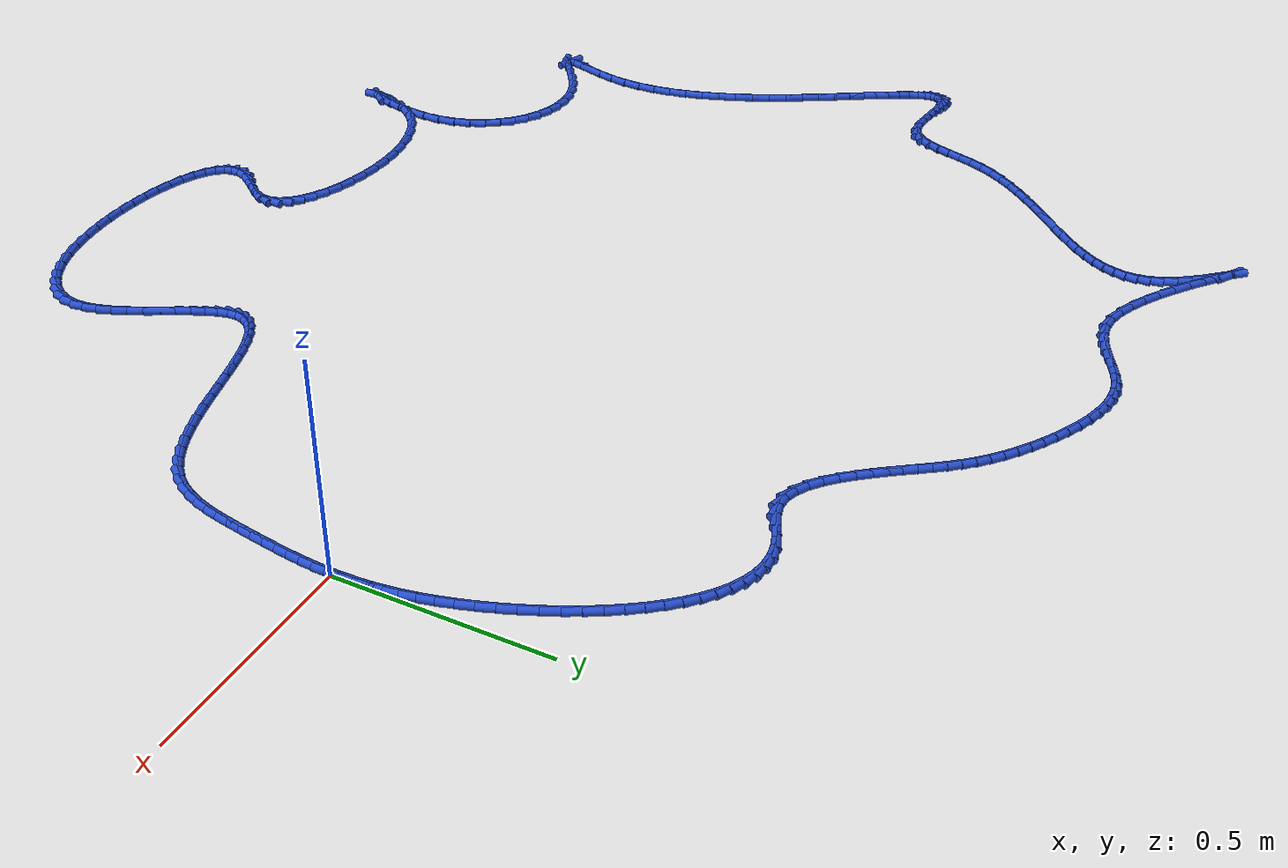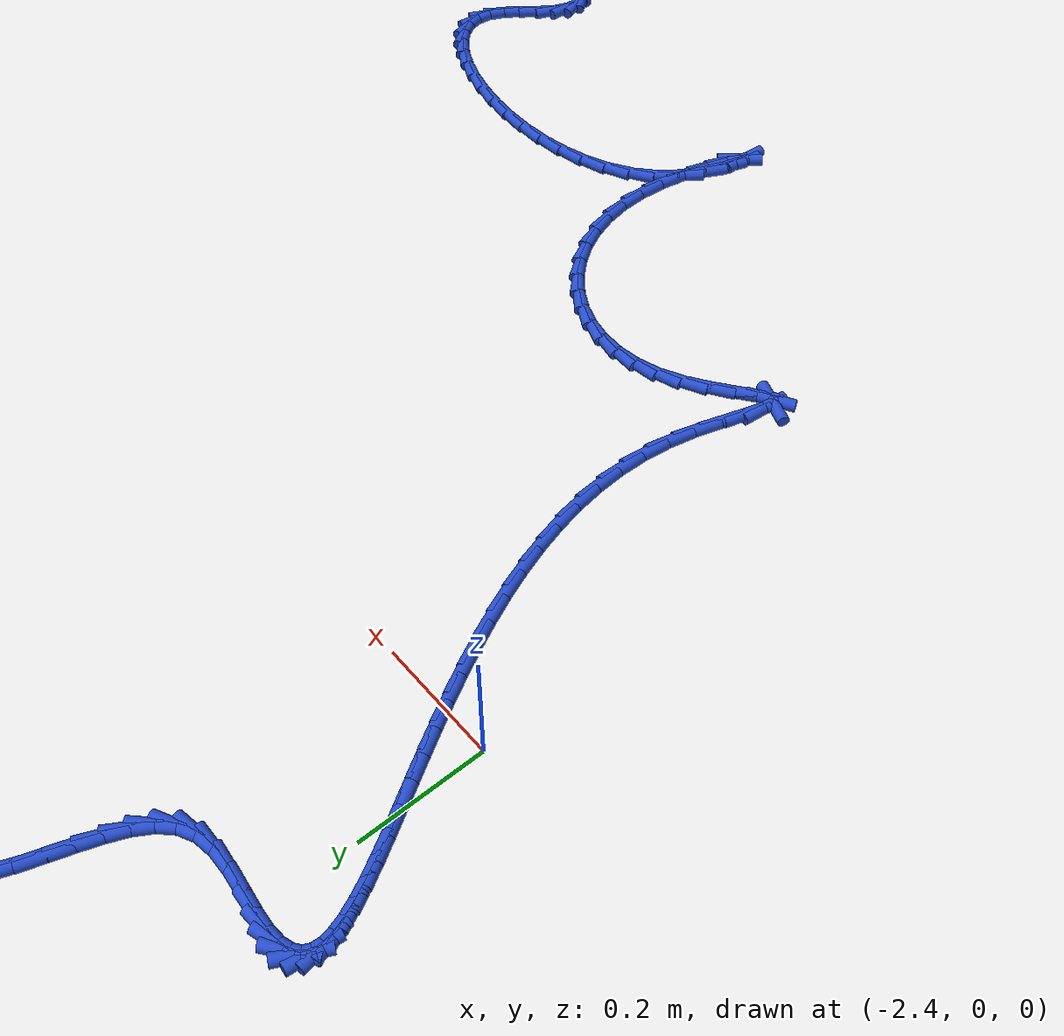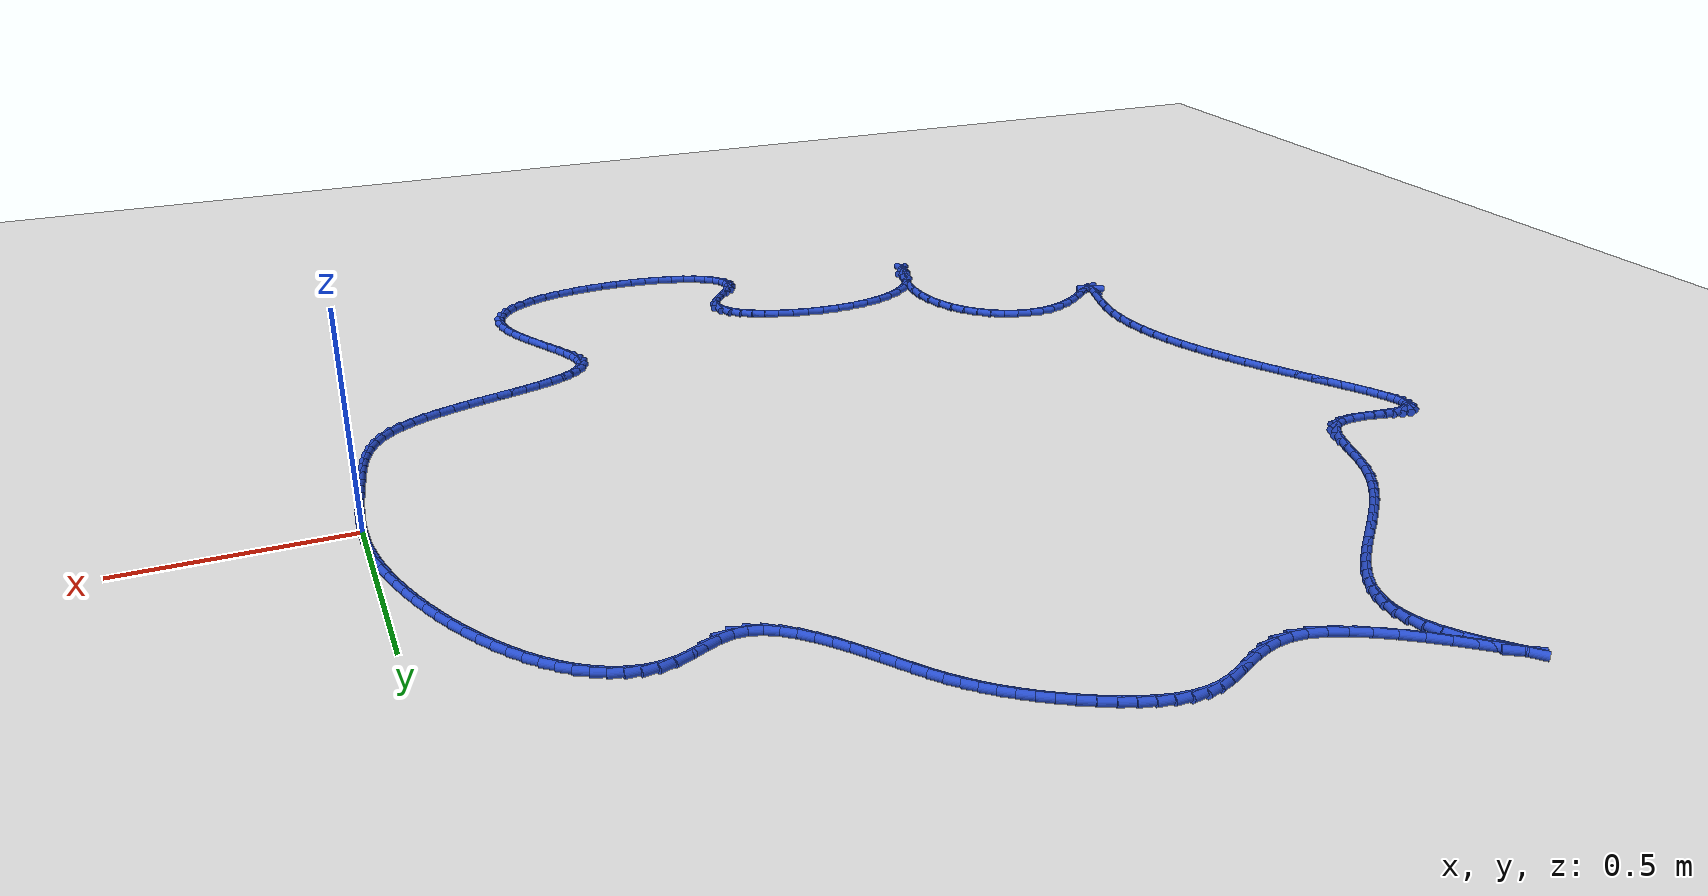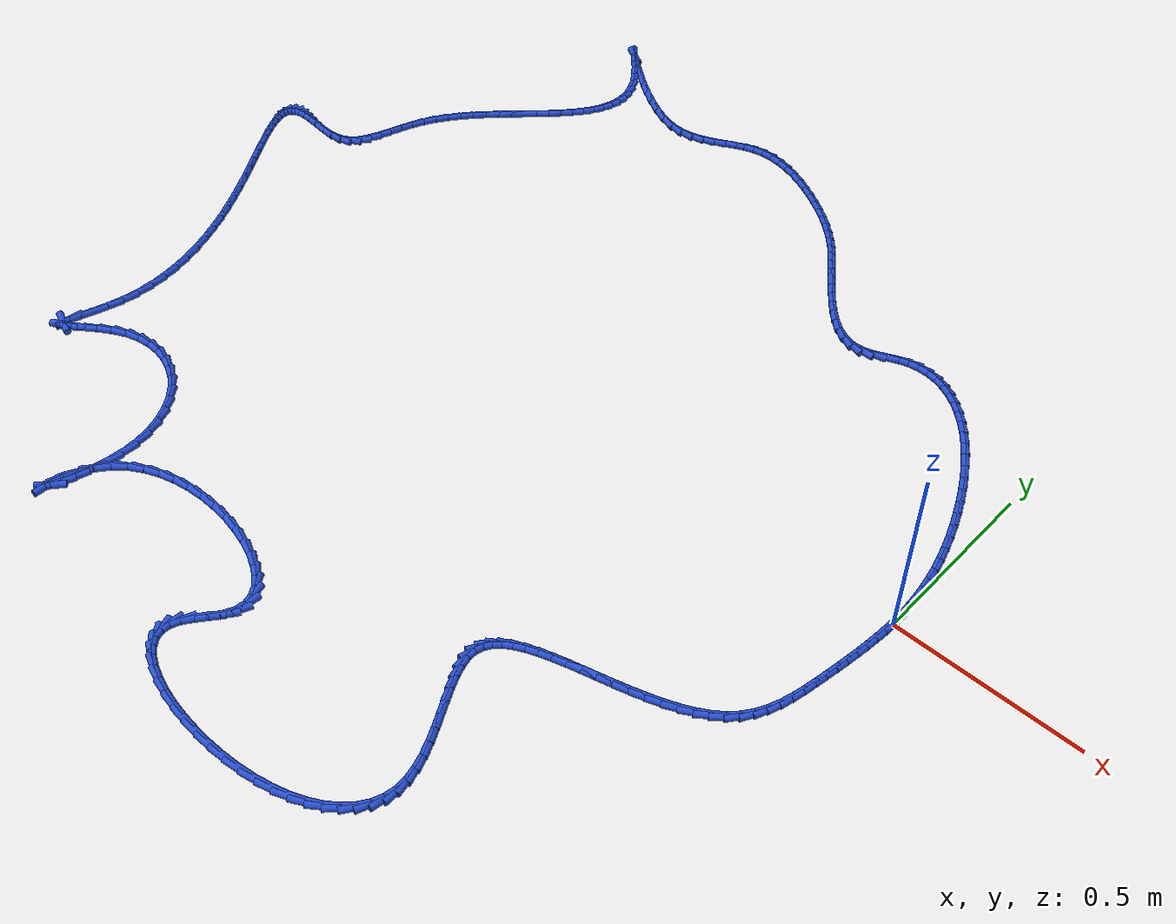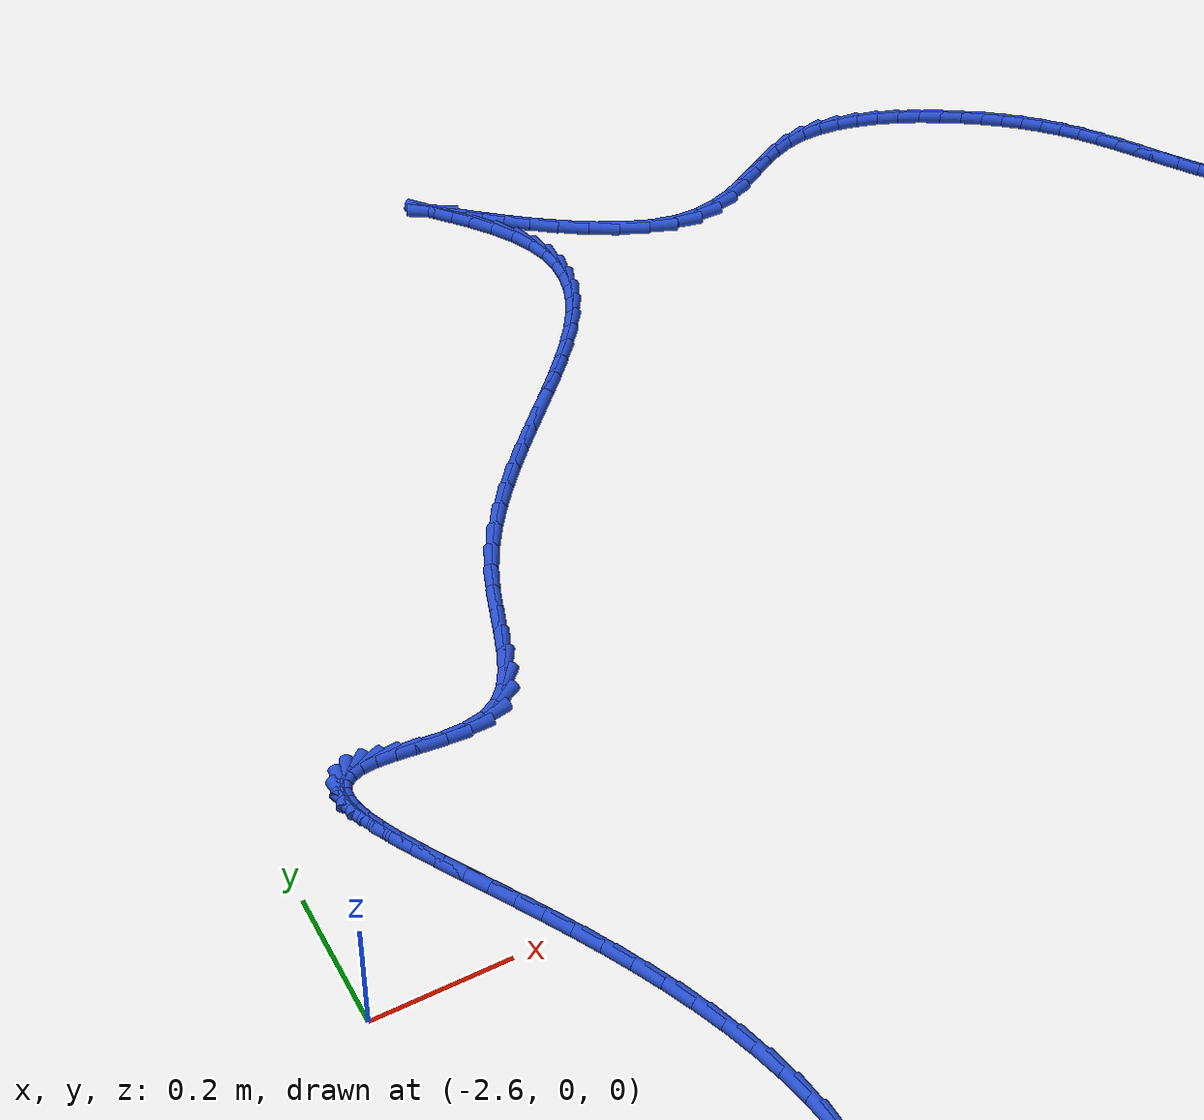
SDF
<sdf version="1.6">
 <world name="default">
  <light name="sun" type="directional">
   <pose>0 0 10 0 -0 0</pose>
   <diffuse>0.8 0.8 0.8 1</diffuse>
   <specular>0.2 0.2 0.2 1</specular>
   <attenuation>
    <range>1000</range>
    <constant>0.9</constant>
    <linear>0.01</linear>
    <quadratic>0.001</quadratic>
   </attenuation>
   <direction>-0.5 0.1 -0.9</direction>
  </light>
  <model name="ground_plane">
   <static>1</static>
   <link name="link">
    <collision name="collision">
     <geometry><plane><normal>0 0 1</normal><size>100 100</size></plane></geometry>
     <surface><friction><ode><mu>100</mu><mu2>50</mu2></ode></friction></surface>
    </collision>
    <visual name="visual">
     <cast_shadows>0</cast_shadows>
     <geometry><plane><normal>0 0 1</normal><size>100 100</size></plane></geometry>
     <material>
      <script><uri>file://media/materials/scripts/gazebo.material</uri><name>Gazebo/WhiteGlow</name></script>
     </material>
    </visual>
   </link>
  </model>
  <gravity>0 0 -9.8</gravity>
  <magnetic_field>6e-06 2.3e-05 -4.2e-05</magnetic_field>
  <atmosphere type="adiabatic"/>
  <physics name="default_physics" default="0" type="ode">
   <max_step_size>0.001</max_step_size>
   <real_time_factor>1</real_time_factor>
   <real_time_update_rate>1000</real_time_update_rate>
  </physics>
  <scene><ambient>0.4 0.4 0.4 1</ambient><background>0.7 0.7 0.7 1</background><shadows>1</shadows></scene>
  <spherical_coordinates>
   <surface_model>EARTH_WGS84</surface_model>
   <latitude_deg>0</latitude_deg>
   <longitude_deg>0</longitude_deg>
   <elevation>0</elevation>
   <heading_deg>0</heading_deg>
  </spherical_coordinates>
  <model name="line">
   <link name="link_0">
    <pose>0.0 7.632783294297951e-17 0.01 0 1.57 1.5602410785087302</pose>
    <collision name="collision">
     <geometry><cylinder><radius>0.01</radius><length>0.08</length></cylinder></geometry>
    </collision>
    <visual name="visual">
     <material>
      <script><name>Gazebo/Blue</name><uri>file://media/materials/scripts/gazebo.material</uri></script>
     </material>
     <geometry><cylinder><radius>0.01</radius><length>0.08</length></cylinder></geometry>
    </visual>
   </link>
   <link name="link_1">
    <pose>0.0003309990488578508 0.031357552871455974 0.01 0 1.57 -1.5428414407994777</pose>
    <collision name="collision">
     <geometry><cylinder><radius>0.01</radius><length>0.08</length></cylinder></geometry>
    </collision>
    <visual name="visual">
     <material>
      <script><name>Gazebo/Blue</name><uri>file://media/materials/scripts/gazebo.material</uri></script>
     </material>
     <geometry><cylinder><radius>0.01</radius><length>0.08</length></cylinder></geometry>
    </visual>
   </link>
   <link name="link_2">
    <pose>-0.0005450256816263664 0.06268647767572658 0.01 0 1.57 -1.5022833746286473</pose>
    <collision name="collision">
     <geometry><cylinder><radius>0.01</radius><length>0.08</length></cylinder></geometry>
    </collision>
    <visual name="visual">
     <material>
      <script><name>Gazebo/Blue</name><uri>file://media/materials/scripts/gazebo.material</uri></script>
     </material>
     <geometry><cylinder><radius>0.01</radius><length>0.08</length></cylinder></geometry>
    </visual>
   </link>
   <link name="link_3">
    <pose>-0.00270702243128811 0.09419311693658512 0.01 0 1.57 -1.4606500215840132</pose>
    <collision name="collision">
     <geometry><cylinder><radius>0.01</radius><length>0.08</length></cylinder></geometry>
    </collision>
    <visual name="visual">
     <material>
      <script><name>Gazebo/Blue</name><uri>file://media/materials/scripts/gazebo.material</uri></script>
     </material>
     <geometry><cylinder><radius>0.01</radius><length>0.08</length></cylinder></geometry>
    </visual>
   </link>
   <link name="link_4">
    <pose>-0.006233939439962836 0.12608381317780482 0.01 0 1.57 -1.4189382596962705</pose>
    <collision name="collision">
     <geometry><cylinder><radius>0.01</radius><length>0.08</length></cylinder></geometry>
    </collision>
    <visual name="visual">
     <material>
      <script><name>Gazebo/Blue</name><uri>file://media/materials/scripts/gazebo.material</uri></script>
     </material>
     <geometry><cylinder><radius>0.01</radius><length>0.08</length></cylinder></geometry>
    </visual>
   </link>
   <link name="link_5">
    <pose>-0.011204724947485999 0.1585649089231589 0.01 0 1.57 -1.3780849845815055</pose>
    <collision name="collision">
     <geometry><cylinder><radius>0.01</radius><length>0.08</length></cylinder></geometry>
    </collision>
    <visual name="visual">
     <material>
      <script><name>Gazebo/Blue</name><uri>file://media/materials/scripts/gazebo.material</uri></script>
     </material>
     <geometry><cylinder><radius>0.01</radius><length>0.08</length></cylinder></geometry>
    </visual>
   </link>
   <link name="link_6">
    <pose>-0.01769832719369307 0.19184274669642065 0.01 0 1.57 -1.3388968363359433</pose>
    <collision name="collision">
     <geometry><cylinder><radius>0.01</radius><length>0.08</length></cylinder></geometry>
    </collision>
    <visual name="visual">
     <material>
      <script><name>Gazebo/Blue</name><uri>file://media/materials/scripts/gazebo.material</uri></script>
     </material>
     <geometry><cylinder><radius>0.01</radius><length>0.08</length></cylinder></geometry>
    </visual>
   </link>
   <link name="link_7">
    <pose>-0.025793694418419492 0.22612366902136324 0.01 0 1.57 -1.3019834450015169</pose>
    <collision name="collision">
     <geometry><cylinder><radius>0.01</radius><length>0.08</length></cylinder></geometry>
    </collision>
    <visual name="visual">
     <material>
      <script><name>Gazebo/Blue</name><uri>file://media/materials/scripts/gazebo.material</uri></script>
     </material>
     <geometry><cylinder><radius>0.01</radius><length>0.08</length></cylinder></geometry>
    </visual>
   </link>
   <link name="link_8">
    <pose>-0.035554027074187616 0.26155388031296817 0.01 0 1.57 -1.2671677220886497</pose>
    <collision name="collision">
     <geometry><cylinder><radius>0.01</radius><length>0.08</length></cylinder></geometry>
    </collision>
    <visual name="visual">
     <material>
      <script><name>Gazebo/Blue</name><uri>file://media/materials/scripts/gazebo.material</uri></script>
     </material>
     <geometry><cylinder><radius>0.01</radius><length>0.08</length></cylinder></geometry>
    </visual>
   </link>
   <link name="link_9">
    <pose>-0.04694953542879025 0.29792447136075006 0.01 0 1.57 -1.2334802067420967</pose>
    <collision name="collision">
     <geometry><cylinder><radius>0.01</radius><length>0.08</length></cylinder></geometry>
    </collision>
    <visual name="visual">
     <material>
      <script><name>Gazebo/Blue</name><uri>file://media/materials/scripts/gazebo.material</uri></script>
     </material>
     <geometry><cylinder><radius>0.01</radius><length>0.08</length></cylinder></geometry>
    </visual>
   </link>
   <link name="link_10">
    <pose>-0.05991641804499858 0.33489664806461306 0.01 0 1.57 -1.2000400107824165</pose>
    <collision name="collision">
     <geometry><cylinder><radius>0.01</radius><length>0.08</length></cylinder></geometry>
    </collision>
    <visual name="visual">
     <material>
      <script><name>Gazebo/Blue</name><uri>file://media/materials/scripts/gazebo.material</uri></script>
     </material>
     <geometry><cylinder><radius>0.01</radius><length>0.08</length></cylinder></geometry>
    </visual>
   </link>
   <link name="link_11">
    <pose>-0.07439082285938078 0.372131422991642 0.01 0 1.57 -1.1660625085651972</pose>
    <collision name="collision">
     <geometry><cylinder><radius>0.01</radius><length>0.08</length></cylinder></geometry>
    </collision>
    <visual name="visual">
     <material>
      <script><name>Gazebo/Blue</name><uri>file://media/materials/scripts/gazebo.material</uri></script>
     </material>
     <geometry><cylinder><radius>0.01</radius><length>0.08</length></cylinder></geometry>
    </visual>
   </link>
   <link name="link_12">
    <pose>-0.09030889780850501 0.4092898087089221 0.01 0 1.57 -1.1307963304815274</pose>
    <collision name="collision">
     <geometry><cylinder><radius>0.01</radius><length>0.08</length></cylinder></geometry>
    </collision>
    <visual name="visual">
     <material>
      <script><name>Gazebo/Blue</name><uri>file://media/materials/scripts/gazebo.material</uri></script>
     </material>
     <geometry><cylinder><radius>0.01</radius><length>0.08</length></cylinder></geometry>
    </visual>
   </link>
   <link name="link_13">
    <pose>-0.10760679082893934 0.44603281778353854 0.01 0 1.57 -1.0934719313543426</pose>
    <collision name="collision">
     <geometry><cylinder><radius>0.01</radius><length>0.08</length></cylinder></geometry>
    </collision>
    <visual name="visual">
     <material>
      <script><name>Gazebo/Blue</name><uri>file://media/materials/scripts/gazebo.material</uri></script>
     </material>
     <geometry><cylinder><radius>0.01</radius><length>0.08</length></cylinder></geometry>
    </visual>
   </link>
   <link name="link_14">
    <pose>-0.12622064985725204 0.4820214627825767 0.01 0 1.57 -1.053254516101011</pose>
    <collision name="collision">
     <geometry><cylinder><radius>0.01</radius><length>0.08</length></cylinder></geometry>
    </collision>
    <visual name="visual">
     <material>
      <script><name>Gazebo/Blue</name><uri>file://media/materials/scripts/gazebo.material</uri></script>
     </material>
     <geometry><cylinder><radius>0.01</radius><length>0.08</length></cylinder></geometry>
    </visual>
   </link>
   <link name="link_15">
    <pose>-0.14608662283001117 0.5169167562731214 0.01 0 1.57 -1.009196533418702</pose>
    <collision name="collision">
     <geometry><cylinder><radius>0.01</radius><length>0.08</length></cylinder></geometry>
    </collision>
    <visual name="visual">
     <material>
      <script><name>Gazebo/Blue</name><uri>file://media/materials/scripts/gazebo.material</uri></script>
     </material>
     <geometry><cylinder><radius>0.01</radius><length>0.08</length></cylinder></geometry>
    </visual>
   </link>
   <link name="link_16">
    <pose>-0.16714085768378495 0.5503797108222581 0.01 0 1.57 -0.9601867418515324</pose>
    <collision name="collision">
     <geometry><cylinder><radius>0.01</radius><length>0.08</length></cylinder></geometry>
    </collision>
    <visual name="visual">
     <material>
      <script><name>Gazebo/Blue</name><uri>file://media/materials/scripts/gazebo.material</uri></script>
     </material>
     <geometry><cylinder><radius>0.01</radius><length>0.08</length></cylinder></geometry>
    </visual>
   </link>
   <link name="link_17">
    <pose>-0.18931950235514144 0.582071338997072 0.01 0 1.57 -0.9048952084887715</pose>
    <collision name="collision">
     <geometry><cylinder><radius>0.01</radius><length>0.08</length></cylinder></geometry>
    </collision>
    <visual name="visual">
     <material>
      <script><name>Gazebo/Blue</name><uri>file://media/materials/scripts/gazebo.material</uri></script>
     </material>
     <geometry><cylinder><radius>0.01</radius><length>0.08</length></cylinder></geometry>
    </visual>
   </link>
   <link name="link_18">
    <pose>-0.21255870478064887 0.6116526533646479 0.01 0 1.57 -0.8417181817801344</pose>
    <collision name="collision">
     <geometry><cylinder><radius>0.01</radius><length>0.08</length></cylinder></geometry>
    </collision>
    <visual name="visual">
     <material>
      <script><name>Gazebo/Blue</name><uri>file://media/materials/scripts/gazebo.material</uri></script>
     </material>
     <geometry><cylinder><radius>0.01</radius><length>0.08</length></cylinder></geometry>
    </visual>
   </link>
   <link name="link_19">
    <pose>-0.23679461289687537 0.6387846664920713 0.01 0 1.57 -0.7687364886461396</pose>
    <collision name="collision">
     <geometry><cylinder><radius>0.01</radius><length>0.08</length></cylinder></geometry>
    </collision>
    <visual name="visual">
     <material>
      <script><name>Gazebo/Blue</name><uri>file://media/materials/scripts/gazebo.material</uri></script>
     </material>
     <geometry><cylinder><radius>0.01</radius><length>0.08</length></cylinder></geometry>
    </visual>
   </link>
   <link name="link_20">
    <pose>-0.26196337464038905 0.6631283909464273 0.01 0 1.57 -0.6837206920881425</pose>
    <collision name="collision">
     <geometry><cylinder><radius>0.01</radius><length>0.08</length></cylinder></geometry>
    </collision>
    <visual name="visual">
     <material>
      <script><name>Gazebo/Blue</name><uri>file://media/materials/scripts/gazebo.material</uri></script>
     </material>
     <geometry><cylinder><radius>0.01</radius><length>0.08</length></cylinder></geometry>
    </visual>
   </link>
   <link name="link_21">
    <pose>-0.2880011379477582 0.6843448392948013 0.01 0 1.57 -0.584251224668055</pose>
    <collision name="collision">
     <geometry><cylinder><radius>0.01</radius><length>0.08</length></cylinder></geometry>
    </collision>
    <visual name="visual">
     <material>
      <script><name>Gazebo/Blue</name><uri>file://media/materials/scripts/gazebo.material</uri></script>
     </material>
     <geometry><cylinder><radius>0.01</radius><length>0.08</length></cylinder></geometry>
    </visual>
   </link>
   <link name="link_22">
    <pose>-0.3148440507555509 0.702095024104278 0.01 0 1.57 -0.46807013256029634</pose>
    <collision name="collision">
     <geometry><cylinder><radius>0.01</radius><length>0.08</length></cylinder></geometry>
    </collision>
    <visual name="visual">
     <material>
      <script><name>Gazebo/Blue</name><uri>file://media/materials/scripts/gazebo.material</uri></script>
     </material>
     <geometry><cylinder><radius>0.01</radius><length>0.08</length></cylinder></geometry>
    </visual>
   </link>
   <link name="link_23">
    <pose>-0.3424282610003351 0.716039957941943 0.01 0 1.57 -0.33380709018294313</pose>
    <collision name="collision">
     <geometry><cylinder><radius>0.01</radius><length>0.08</length></cylinder></geometry>
    </collision>
    <visual name="visual">
     <material>
      <script><name>Gazebo/Blue</name><uri>file://media/materials/scripts/gazebo.material</uri></script>
     </material>
     <geometry><cylinder><radius>0.01</radius><length>0.08</length></cylinder></geometry>
    </visual>
   </link>
   <link name="link_24">
    <pose>-0.3706899166186793 0.7258406533748811 0.01 0 1.57 -0.1821128685247869</pose>
    <collision name="collision">
     <geometry><cylinder><radius>0.01</radius><length>0.08</length></cylinder></geometry>
    </collision>
    <visual name="visual">
     <material>
      <script><name>Gazebo/Blue</name><uri>file://media/materials/scripts/gazebo.material</uri></script>
     </material>
     <geometry><cylinder><radius>0.01</radius><length>0.08</length></cylinder></geometry>
    </visual>
   </link>
   <link name="link_25">
    <pose>-0.3995651655471514 0.7311581229701778 0.01 0 1.57 -0.016829557566478415</pose>
    <collision name="collision">
     <geometry><cylinder><radius>0.01</radius><length>0.08</length></cylinder></geometry>
    </collision>
    <visual name="visual">
     <material>
      <script><name>Gazebo/Blue</name><uri>file://media/materials/scripts/gazebo.material</uri></script>
     </material>
     <geometry><cylinder><radius>0.01</radius><length>0.08</length></cylinder></geometry>
    </visual>
   </link>
   <link name="link_26">
    <pose>-0.4289901557223196 0.731653379294918 0.01 0 1.57 0.15474770349344974</pose>
    <collision name="collision">
     <geometry><cylinder><radius>0.01</radius><length>0.08</length></cylinder></geometry>
    </collision>
    <visual name="visual">
     <material>
      <script><name>Gazebo/Blue</name><uri>file://media/materials/scripts/gazebo.material</uri></script>
     </material>
     <geometry><cylinder><radius>0.01</radius><length>0.08</length></cylinder></geometry>
    </visual>
   </link>
   <link name="link_27">
    <pose>-0.4589010350807521 0.7269874349161871 0.01 0 1.57 0.3215064868909488</pose>
    <collision name="collision">
     <geometry><cylinder><radius>0.01</radius><length>0.08</length></cylinder></geometry>
    </collision>
    <visual name="visual">
     <material>
      <script><name>Gazebo/Blue</name><uri>file://media/materials/scripts/gazebo.material</uri></script>
     </material>
     <geometry><cylinder><radius>0.01</radius><length>0.08</length></cylinder></geometry>
    </visual>
   </link>
   <link name="link_28">
    <pose>-0.489231217882669 0.7168855984377859 0.01 0 1.57 0.4230516009280961</pose>
    <collision name="collision">
     <geometry><cylinder><radius>0.01</radius><length>0.08</length></cylinder></geometry>
    </collision>
    <visual name="visual">
     <material>
      <script><name>Gazebo/Blue</name><uri>file://media/materials/scripts/gazebo.material</uri></script>
     </material>
     <geometry><cylinder><radius>0.01</radius><length>0.08</length></cylinder></geometry>
    </visual>
   </link>
   <link name="link_29">
    <pose>-0.519827519245681 0.7031099893159112 0.01 0 1.57 0.40942129871275734</pose>
    <collision name="collision">
     <geometry><cylinder><radius>0.01</radius><length>0.08</length></cylinder></geometry>
    </collision>
    <visual name="visual">
     <material>
      <script><name>Gazebo/Blue</name><uri>file://media/materials/scripts/gazebo.material</uri></script>
     </material>
     <geometry><cylinder><radius>0.01</radius><length>0.08</length></cylinder></geometry>
    </visual>
   </link>
   <link name="link_30">
    <pose>-0.5504344763212026 0.6898283036121865 0.01 0 1.57 0.27244731959582164</pose>
    <collision name="collision">
     <geometry><cylinder><radius>0.01</radius><length>0.08</length></cylinder></geometry>
    </collision>
    <visual name="visual">
     <material>
      <script><name>Gazebo/Blue</name><uri>file://media/materials/scripts/gazebo.material</uri></script>
     </material>
     <geometry><cylinder><radius>0.01</radius><length>0.08</length></cylinder></geometry>
    </visual>
   </link>
   <link name="link_31">
    <pose>-0.5807907295750022 0.6813469273677638 0.01 0 1.57 -0.0019705620650321077</pose>
    <collision name="collision">
     <geometry><cylinder><radius>0.01</radius><length>0.08</length></cylinder></geometry>
    </collision>
    <visual name="visual">
     <material>
      <script><name>Gazebo/Blue</name><uri>file://media/materials/scripts/gazebo.material</uri></script>
     </material>
     <geometry><cylinder><radius>0.01</radius><length>0.08</length></cylinder></geometry>
    </visual>
   </link>
   <link name="link_32">
    <pose>-0.6106427766690227 0.6814057527554728 0.01 0 1.57 -0.2867981203086742</pose>
    <collision name="collision">
     <geometry><cylinder><radius>0.01</radius><length>0.08</length></cylinder></geometry>
    </collision>
    <visual name="visual">
     <material>
      <script><name>Gazebo/Blue</name><uri>file://media/materials/scripts/gazebo.material</uri></script>
     </material>
     <geometry><cylinder><radius>0.01</radius><length>0.08</length></cylinder></geometry>
    </visual>
   </link>
   <link name="link_33">
    <pose>-0.6397890279914353 0.6900018302974791 0.01 0 1.57 -0.5047179763512967</pose>
    <collision name="collision">
     <geometry><cylinder><radius>0.01</radius><length>0.08</length></cylinder></geometry>
    </collision>
    <visual name="visual">
     <material>
      <script><name>Gazebo/Blue</name><uri>file://media/materials/scripts/gazebo.material</uri></script>
     </material>
     <geometry><cylinder><radius>0.01</radius><length>0.08</length></cylinder></geometry>
    </visual>
   </link>
   <link name="link_34">
    <pose>-0.6680489531455344 0.7056138678432118 0.01 0 1.57 -0.6599458796858335</pose>
    <collision name="collision">
     <geometry><cylinder><radius>0.01</radius><length>0.08</length></cylinder></geometry>
    </collision>
    <visual name="visual">
     <material>
      <script><name>Gazebo/Blue</name><uri>file://media/materials/scripts/gazebo.material</uri></script>
     </material>
     <geometry><cylinder><radius>0.01</radius><length>0.08</length></cylinder></geometry>
    </visual>
   </link>
   <link name="link_35">
    <pose>-0.6952420819657715 0.726716230652086 0.01 0 1.57 -0.7681726812389821</pose>
    <collision name="collision">
     <geometry><cylinder><radius>0.01</radius><length>0.08</length></cylinder></geometry>
    </collision>
    <visual name="visual">
     <material>
      <script><name>Gazebo/Blue</name><uri>file://media/materials/scripts/gazebo.material</uri></script>
     </material>
     <geometry><cylinder><radius>0.01</radius><length>0.08</length></cylinder></geometry>
    </visual>
   </link>
   <link name="link_36">
    <pose>-0.7211879442865998 0.7517832839835176 0.01 0 1.57 -0.8427695875988271</pose>
    <collision name="collision">
     <geometry><cylinder><radius>0.01</radius><length>0.08</length></cylinder></geometry>
    </collision>
    <visual name="visual">
     <material>
      <script><name>Gazebo/Blue</name><uri>file://media/materials/scripts/gazebo.material</uri></script>
     </material>
     <geometry><cylinder><radius>0.01</radius><length>0.08</length></cylinder></geometry>
    </visual>
   </link>
   <link name="link_37">
    <pose>-0.7457060699424707 0.7792893930969212 0.01 0 1.57 -0.8923269711345042</pose>
    <collision name="collision">
     <geometry><cylinder><radius>0.01</radius><length>0.08</length></cylinder></geometry>
    </collision>
    <visual name="visual">
     <material>
      <script><name>Gazebo/Blue</name><uri>file://media/materials/scripts/gazebo.material</uri></script>
     </material>
     <geometry><cylinder><radius>0.01</radius><length>0.08</length></cylinder></geometry>
    </visual>
   </link>
   <link name="link_38">
    <pose>-0.7686159887903784 0.8077089233001533 0.01 0 1.57 -0.9228568453196128</pose>
    <collision name="collision">
     <geometry><cylinder><radius>0.01</radius><length>0.08</length></cylinder></geometry>
    </collision>
    <visual name="visual">
     <material>
      <script><name>Gazebo/Blue</name><uri>file://media/materials/scripts/gazebo.material</uri></script>
     </material>
     <geometry><cylinder><radius>0.01</radius><length>0.08</length></cylinder></geometry>
    </visual>
   </link>
   <link name="link_39">
    <pose>-0.7898525569310719 0.8357640644121936 0.01 0 1.57 -0.9411997638317315</pose>
    <collision name="collision">
     <geometry><cylinder><radius>0.01</radius><length>0.08</length></cylinder></geometry>
    </collision>
    <visual name="visual">
     <material>
      <script><name>Gazebo/Blue</name><uri>file://media/materials/scripts/gazebo.material</uri></script>
     </material>
     <geometry><cylinder><radius>0.01</radius><length>0.08</length></cylinder></geometry>
    </visual>
   </link>
   <link name="link_40">
    <pose>-0.8098039276731521 0.8631510964094102 0.01 0 1.57 -0.9474049773456503</pose>
    <collision name="collision">
     <geometry><cylinder><radius>0.01</radius><length>0.08</length></cylinder></geometry>
    </collision>
    <visual name="visual">
     <material>
      <script><name>Gazebo/Blue</name><uri>file://media/materials/scripts/gazebo.material</uri></script>
     </material>
     <geometry><cylinder><radius>0.01</radius><length>0.08</length></cylinder></geometry>
    </visual>
   </link>
   <link name="link_41">
    <pose>-0.8289696113167944 0.8898055942551454 0.01 0 1.57 -0.9401301825323694</pose>
    <collision name="collision">
     <geometry><cylinder><radius>0.01</radius><length>0.08</length></cylinder></geometry>
    </collision>
    <visual name="visual">
     <material>
      <script><name>Gazebo/Blue</name><uri>file://media/materials/scripts/gazebo.material</uri></script>
     </material>
     <geometry><cylinder><radius>0.01</radius><length>0.08</length></cylinder></geometry>
    </visual>
   </link>
   <link name="link_42">
    <pose>-0.8478491181621721 0.9156631329127393 0.01 0 1.57 -0.9185019148888919</pose>
    <collision name="collision">
     <geometry><cylinder><radius>0.01</radius><length>0.08</length></cylinder></geometry>
    </collision>
    <visual name="visual">
     <material>
      <script><name>Gazebo/Blue</name><uri>file://media/materials/scripts/gazebo.material</uri></script>
     </material>
     <geometry><cylinder><radius>0.01</radius><length>0.08</length></cylinder></geometry>
    </visual>
   </link>
   <link name="link_43">
    <pose>-0.8669419585094603 0.9406592873455332 0.01 0 1.57 -0.8822917669134398</pose>
    <collision name="collision">
     <geometry><cylinder><radius>0.01</radius><length>0.08</length></cylinder></geometry>
    </collision>
    <visual name="visual">
     <material>
      <script><name>Gazebo/Blue</name><uri>file://media/materials/scripts/gazebo.material</uri></script>
     </material>
     <geometry><cylinder><radius>0.01</radius><length>0.08</length></cylinder></geometry>
    </visual>
   </link>
   <link name="link_44">
    <pose>-0.886747642658833 0.9647296325168679 0.01 0 1.57 -0.8321746514424951</pose>
    <collision name="collision">
     <geometry><cylinder><radius>0.01</radius><length>0.08</length></cylinder></geometry>
    </collision>
    <visual name="visual">
     <material>
      <script><name>Gazebo/Blue</name><uri>file://media/materials/scripts/gazebo.material</uri></script>
     </material>
     <geometry><cylinder><radius>0.01</radius><length>0.08</length></cylinder></geometry>
    </visual>
   </link>
   <link name="link_45">
    <pose>-0.9077638565992792 0.9878100371384392 0.01 0 1.57 -0.7745334515542378</pose>
    <collision name="collision">
     <geometry><cylinder><radius>0.01</radius><length>0.08</length></cylinder></geometry>
    </collision>
    <visual name="visual">
     <material>
      <script><name>Gazebo/Blue</name><uri>file://media/materials/scripts/gazebo.material</uri></script>
     </material>
     <geometry><cylinder><radius>0.01</radius><length>0.08</length></cylinder></geometry>
    </visual>
   </link>
   <link name="link_46">
    <pose>-0.9303043527400612 1.0098659866818702 0.01 0 1.57 -0.7192289510089606</pose>
    <collision name="collision">
     <geometry><cylinder><radius>0.01</radius><length>0.08</length></cylinder></geometry>
    </collision>
    <visual name="visual">
     <material>
      <script><name>Gazebo/Blue</name><uri>file://media/materials/scripts/gazebo.material</uri></script>
     </material>
     <geometry><cylinder><radius>0.01</radius><length>0.08</length></cylinder></geometry>
    </visual>
   </link>
   <link name="link_47">
    <pose>-0.9543439187659414 1.0309175463039333 0.01 0 1.57 -0.6673157131287292</pose>
    <collision name="collision">
     <geometry><cylinder><radius>0.01</radius><length>0.08</length></cylinder></geometry>
    </collision>
    <visual name="visual">
     <material>
      <script><name>Gazebo/Blue</name><uri>file://media/materials/scripts/gazebo.material</uri></script>
     </material>
     <geometry><cylinder><radius>0.01</radius><length>0.08</length></cylinder></geometry>
    </visual>
   </link>
   <link name="link_48">
    <pose>-0.9798208306211499 1.0509906602371812 0.01 0 1.57 -0.6187740854668721</pose>
    <collision name="collision">
     <geometry><cylinder><radius>0.01</radius><length>0.08</length></cylinder></geometry>
    </collision>
    <visual name="visual">
     <material>
      <script><name>Gazebo/Blue</name><uri>file://media/materials/scripts/gazebo.material</uri></script>
     </material>
     <geometry><cylinder><radius>0.01</radius><length>0.08</length></cylinder></geometry>
    </visual>
   </link>
   <link name="link_49">
    <pose>-1.0066733642499168 1.0701112727141662 0.01 0 1.57 -0.5735215700252003</pose>
    <collision name="collision">
     <geometry><cylinder><radius>0.01</radius><length>0.08</length></cylinder></geometry>
    </collision>
    <visual name="visual">
     <material>
      <script><name>Gazebo/Blue</name><uri>file://media/materials/scripts/gazebo.material</uri></script>
     </material>
     <geometry><cylinder><radius>0.01</radius><length>0.08</length></cylinder></geometry>
    </visual>
   </link>
   <link name="link_50">
    <pose>-1.0348397955964728 1.0883053279674415 0.01 0 1.57 -0.5314305802721714</pose>
    <collision name="collision">
     <geometry><cylinder><radius>0.01</radius><length>0.08</length></cylinder></geometry>
    </collision>
    <visual name="visual">
     <material>
      <script><name>Gazebo/Blue</name><uri>file://media/materials/scripts/gazebo.material</uri></script>
     </material>
     <geometry><cylinder><radius>0.01</radius><length>0.08</length></cylinder></geometry>
    </visual>
   </link>
   <link name="link_51">
    <pose>-1.0642584006050473 1.105598770229559 0.01 0 1.57 -0.4904294313540992</pose>
    <collision name="collision">
     <geometry><cylinder><radius>0.01</radius><length>0.08</length></cylinder></geometry>
    </collision>
    <visual name="visual">
     <material>
      <script><name>Gazebo/Blue</name><uri>file://media/materials/scripts/gazebo.material</uri></script>
     </material>
     <geometry><cylinder><radius>0.01</radius><length>0.08</length></cylinder></geometry>
    </visual>
   </link>
   <link name="link_52">
    <pose>-1.0948277662881647 1.1219209736396423 0.01 0 1.57 -0.44204986152496695</pose>
    <collision name="collision">
     <geometry><cylinder><radius>0.01</radius><length>0.08</length></cylinder></geometry>
    </collision>
    <visual name="visual">
     <material>
      <script><name>Gazebo/Blue</name><uri>file://media/materials/scripts/gazebo.material</uri></script>
     </material>
     <geometry><cylinder><radius>0.01</radius><length>0.08</length></cylinder></geometry>
    </visual>
   </link>
   <link name="link_53">
    <pose>-1.1262854456209372 1.1368094884360602 0.01 0 1.57 -0.3825475306583266</pose>
    <collision name="collision">
     <geometry><cylinder><radius>0.01</radius><length>0.08</length></cylinder></geometry>
    </collision>
    <visual name="visual">
     <material>
      <script><name>Gazebo/Blue</name><uri>file://media/materials/scripts/gazebo.material</uri></script>
     </material>
     <geometry><cylinder><radius>0.01</radius><length>0.08</length></cylinder></geometry>
    </visual>
   </link>
   <link name="link_54">
    <pose>-1.1583281553412457 1.1497025031692982 0.01 0 1.57 -0.3094749751331333</pose>
    <collision name="collision">
     <geometry><cylinder><radius>0.01</radius><length>0.08</length></cylinder></geometry>
    </collision>
    <visual name="visual">
     <material>
      <script><name>Gazebo/Blue</name><uri>file://media/materials/scripts/gazebo.material</uri></script>
     </material>
     <geometry><cylinder><radius>0.01</radius><length>0.08</length></cylinder></geometry>
    </visual>
   </link>
   <link name="link_55">
    <pose>-1.1906526121826588 1.160038206379347 0.01 0 1.57 -0.21979419534022454</pose>
    <collision name="collision">
     <geometry><cylinder><radius>0.01</radius><length>0.08</length></cylinder></geometry>
    </collision>
    <visual name="visual">
     <material>
      <script><name>Gazebo/Blue</name><uri>file://media/materials/scripts/gazebo.material</uri></script>
     </material>
     <geometry><cylinder><radius>0.01</radius><length>0.08</length></cylinder></geometry>
    </visual>
   </link>
   <link name="link_56">
    <pose>-1.2229555328787454 1.1672547866061973 0.01 0 1.57 -0.1101173365197323</pose>
    <collision name="collision">
     <geometry><cylinder><radius>0.01</radius><length>0.08</length></cylinder></geometry>
    </collision>
    <visual name="visual">
     <material>
      <script><name>Gazebo/Blue</name><uri>file://media/materials/scripts/gazebo.material</uri></script>
     </material>
     <geometry><cylinder><radius>0.01</radius><length>0.08</length></cylinder></geometry>
    </visual>
   </link>
   <link name="link_57">
    <pose>-1.2549336341630724 1.1707904323898384 0.01 0 1.57 0.02255120510608637</pose>
    <collision name="collision">
     <geometry><cylinder><radius>0.01</radius><length>0.08</length></cylinder></geometry>
    </collision>
    <visual name="visual">
     <material>
      <script><name>Gazebo/Blue</name><uri>file://media/materials/scripts/gazebo.material</uri></script>
     </material>
     <geometry><cylinder><radius>0.01</radius><length>0.08</length></cylinder></geometry>
    </visual>
   </link>
   <link name="link_58">
    <pose>-1.2862836327692087 1.1700833322702615 0.01 0 1.57 0.17903485937706692</pose>
    <collision name="collision">
     <geometry><cylinder><radius>0.01</radius><length>0.08</length></cylinder></geometry>
    </collision>
    <visual name="visual">
     <material>
      <script><name>Gazebo/Blue</name><uri>file://media/materials/scripts/gazebo.material</uri></script>
     </material>
     <geometry><cylinder><radius>0.01</radius><length>0.08</length></cylinder></geometry>
    </visual>
   </link>
   <link name="link_59">
    <pose>-1.3167045520017633 1.1645779792830386 0.01 0 1.57 0.3322416490544961</pose>
    <collision name="collision">
     <geometry><cylinder><radius>0.01</radius><length>0.08</length></cylinder></geometry>
    </collision>
    <visual name="visual">
     <material>
      <script><name>Gazebo/Blue</name><uri>file://media/materials/scripts/gazebo.material</uri></script>
     </material>
     <geometry><cylinder><radius>0.01</radius><length>0.08</length></cylinder></geometry>
    </visual>
   </link>
   <link name="link_60">
    <pose>-1.3461511879102448 1.154417964003633 0.01 0 1.57 0.43247679287994784</pose>
    <collision name="collision">
     <geometry><cylinder><radius>0.01</radius><length>0.08</length></cylinder></geometry>
    </collision>
    <visual name="visual">
     <material>
      <script><name>Gazebo/Blue</name><uri>file://media/materials/scripts/gazebo.material</uri></script>
     </material>
     <geometry><cylinder><radius>0.01</radius><length>0.08</length></cylinder></geometry>
    </visual>
   </link>
   <link name="link_61">
    <pose>-1.3750630106778203 1.1410716252508115 0.01 0 1.57 0.47689710724915846</pose>
    <collision name="collision">
     <geometry><cylinder><radius>0.01</radius><length>0.08</length></cylinder></geometry>
    </collision>
    <visual name="visual">
     <material>
      <script><name>Gazebo/Blue</name><uri>file://media/materials/scripts/gazebo.material</uri></script>
     </material>
     <geometry><cylinder><radius>0.01</radius><length>0.08</length></cylinder></geometry>
    </visual>
   </link>
   <link name="link_62">
    <pose>-1.4039335274966636 1.1261549999105207 0.01 0 1.57 0.46934739829801453</pose>
    <collision name="collision">
     <geometry><cylinder><radius>0.01</radius><length>0.08</length></cylinder></geometry>
    </collision>
    <visual name="visual">
     <material>
      <script><name>Gazebo/Blue</name><uri>file://media/materials/scripts/gazebo.material</uri></script>
     </material>
     <geometry><cylinder><radius>0.01</radius><length>0.08</length></cylinder></geometry>
    </visual>
   </link>
   <link name="link_63">
    <pose>-1.4332562455589477 1.1112841248687049 0.01 0 1.57 0.41148530625701557</pose>
    <collision name="collision">
     <geometry><cylinder><radius>0.01</radius><length>0.08</length></cylinder></geometry>
    </collision>
    <visual name="visual">
     <material>
      <script><name>Gazebo/Blue</name><uri>file://media/materials/scripts/gazebo.material</uri></script>
     </material>
     <geometry><cylinder><radius>0.01</radius><length>0.08</length></cylinder></geometry>
    </visual>
   </link>
   <link name="link_64">
    <pose>-1.4635246720568456 1.0980750370113104 0.01 0 1.57 0.30353482138505744</pose>
    <collision name="collision">
     <geometry><cylinder><radius>0.01</radius><length>0.08</length></cylinder></geometry>
    </collision>
    <visual name="visual">
     <material>
      <script><name>Gazebo/Blue</name><uri>file://media/materials/scripts/gazebo.material</uri></script>
     </material>
     <geometry><cylinder><radius>0.01</radius><length>0.08</length></cylinder></geometry>
    </visual>
   </link>
   <link name="link_65">
    <pose>-1.4952323141825306 1.088143773224283 0.01 0 1.57 0.14863840914152304</pose>
    <collision name="collision">
     <geometry><cylinder><radius>0.01</radius><length>0.08</length></cylinder></geometry>
    </collision>
    <visual name="visual">
     <material>
      <script><name>Gazebo/Blue</name><uri>file://media/materials/scripts/gazebo.material</uri></script>
     </material>
     <geometry><cylinder><radius>0.01</radius><length>0.08</length></cylinder></geometry>
    </visual>
   </link>
   <link name="link_66">
    <pose>-1.5288726791281757 1.0831063703935677 0.01 0 1.57 -0.04080445315504187</pose>
    <collision name="collision">
     <geometry><cylinder><radius>0.01</radius><length>0.08</length></cylinder></geometry>
    </collision>
    <visual name="visual">
     <material>
      <script><name>Gazebo/Blue</name><uri>file://media/materials/scripts/gazebo.material</uri></script>
     </material>
     <geometry><cylinder><radius>0.01</radius><length>0.08</length></cylinder></geometry>
    </visual>
   </link>
   <link name="link_67">
    <pose>-1.5649392740859536 1.084578865405111 0.01 0 1.57 -0.2337654186073965</pose>
    <collision name="collision">
     <geometry><cylinder><radius>0.01</radius><length>0.08</length></cylinder></geometry>
    </collision>
    <visual name="visual">
     <material>
      <script><name>Gazebo/Blue</name><uri>file://media/materials/scripts/gazebo.material</uri></script>
     </material>
     <geometry><cylinder><radius>0.01</radius><length>0.08</length></cylinder></geometry>
    </visual>
   </link>
   <link name="link_68">
    <pose>-1.6037393155495658 1.0938178822584899 0.01 0 1.57 -0.37672906411097346</pose>
    <collision name="collision">
     <geometry><cylinder><radius>0.01</radius><length>0.08</length></cylinder></geometry>
    </collision>
    <visual name="visual">
     <material>
      <script><name>Gazebo/Blue</name><uri>file://media/materials/scripts/gazebo.material</uri></script>
     </material>
     <geometry><cylinder><radius>0.01</radius><length>0.08</length></cylinder></geometry>
    </visual>
   </link>
   <link name="link_69">
    <pose>-1.6444657523950652 1.1099302750295739 0.01 0 1.57 -0.4747867884725967</pose>
    <collision name="collision">
     <geometry><cylinder><radius>0.01</radius><length>0.08</length></cylinder></geometry>
    </collision>
    <visual name="visual">
     <material>
      <script><name>Gazebo/Blue</name><uri>file://media/materials/scripts/gazebo.material</uri></script>
     </material>
     <geometry><cylinder><radius>0.01</radius><length>0.08</length></cylinder></geometry>
    </visual>
   </link>
   <link name="link_70">
    <pose>-1.6858990548762667 1.1312270978246173 0.01 0 1.57 -0.544703677572929</pose>
    <collision name="collision">
     <geometry><cylinder><radius>0.01</radius><length>0.08</length></cylinder></geometry>
    </collision>
    <visual name="visual">
     <material>
      <script><name>Gazebo/Blue</name><uri>file://media/materials/scripts/gazebo.material</uri></script>
     </material>
     <geometry><cylinder><radius>0.01</radius><length>0.08</length></cylinder></geometry>
    </visual>
   </link>
   <link name="link_71">
    <pose>-1.7268190248066024 1.1560181151197997 0.01 0 1.57 -0.5962721454302685</pose>
    <collision name="collision">
     <geometry><cylinder><radius>0.01</radius><length>0.08</length></cylinder></geometry>
    </collision>
    <visual name="visual">
     <material>
      <script><name>Gazebo/Blue</name><uri>file://media/materials/scripts/gazebo.material</uri></script>
     </material>
     <geometry><cylinder><radius>0.01</radius><length>0.08</length></cylinder></geometry>
    </visual>
   </link>
   <link name="link_72">
    <pose>-1.7660054639995024 1.1826130913912998 0.01 0 1.57 -0.6352219180496846</pose>
    <collision name="collision">
     <geometry><cylinder><radius>0.01</radius><length>0.08</length></cylinder></geometry>
    </collision>
    <visual name="visual">
     <material>
      <script><name>Gazebo/Blue</name><uri>file://media/materials/scripts/gazebo.material</uri></script>
     </material>
     <geometry><cylinder><radius>0.01</radius><length>0.08</length></cylinder></geometry>
    </visual>
   </link>
   <link name="link_73">
    <pose>-1.802238174268398 1.2093217911152956 0.01 0 1.57 -0.6648717432445969</pose>
    <collision name="collision">
     <geometry><cylinder><radius>0.01</radius><length>0.08</length></cylinder></geometry>
    </collision>
    <visual name="visual">
     <material>
      <script><name>Gazebo/Blue</name><uri>file://media/materials/scripts/gazebo.material</uri></script>
     </material>
     <geometry><cylinder><radius>0.01</radius><length>0.08</length></cylinder></geometry>
    </visual>
   </link>
   <link name="link_74">
    <pose>-1.8342969574267207 1.2344539787679671 0.01 0 1.57 -0.6868270817080524</pose>
    <collision name="collision">
     <geometry><cylinder><radius>0.01</radius><length>0.08</length></cylinder></geometry>
    </collision>
    <visual name="visual">
     <material>
      <script><name>Gazebo/Blue</name><uri>file://media/materials/scripts/gazebo.material</uri></script>
     </material>
     <geometry><cylinder><radius>0.01</radius><length>0.08</length></cylinder></geometry>
    </visual>
   </link>
   <link name="link_75">
    <pose>-1.8609616152879005 1.2563194188254925 0.01 0 1.57 -0.7005917761581065</pose>
    <collision name="collision">
     <geometry><cylinder><radius>0.01</radius><length>0.08</length></cylinder></geometry>
    </collision>
    <visual name="visual">
     <material>
      <script><name>Gazebo/Blue</name><uri>file://media/materials/scripts/gazebo.material</uri></script>
     </material>
     <geometry><cylinder><radius>0.01</radius><length>0.08</length></cylinder></geometry>
    </visual>
   </link>
   <link name="link_76">
    <pose>-1.8810119496653688 1.2732278757640503 0.01 0 1.57 -0.6986576947608345</pose>
    <collision name="collision">
     <geometry><cylinder><radius>0.01</radius><length>0.08</length></cylinder></geometry>
    </collision>
    <visual name="visual">
     <material>
      <script><name>Gazebo/Blue</name><uri>file://media/materials/scripts/gazebo.material</uri></script>
     </material>
     <geometry><cylinder><radius>0.01</radius><length>0.08</length></cylinder></geometry>
    </visual>
   </link>
   <link name="link_77">
    <pose>-1.893227762372557 1.2834891140598201 0.01 0 1.57 -0.5467058913655953</pose>
    <collision name="collision">
     <geometry><cylinder><radius>0.01</radius><length>0.08</length></cylinder></geometry>
    </collision>
    <visual name="visual">
     <material>
      <script><name>Gazebo/Blue</name><uri>file://media/materials/scripts/gazebo.material</uri></script>
     </material>
     <geometry><cylinder><radius>0.01</radius><length>0.08</length></cylinder></geometry>
    </visual>
   </link>
   <link name="link_78">
    <pose>-1.8963888552228956 1.28541289818898 0.01 0 1.57 -0.8507442898011937</pose>
    <collision name="collision">
     <geometry><cylinder><radius>0.01</radius><length>0.08</length></cylinder></geometry>
    </collision>
    <visual name="visual">
     <material>
      <script><name>Gazebo/Blue</name><uri>file://media/materials/scripts/gazebo.material</uri></script>
     </material>
     <geometry><cylinder><radius>0.01</radius><length>0.08</length></cylinder></geometry>
    </visual>
   </link>
   <link name="link_79">
    <pose>-1.8892967962554643 1.2773276466880934 0.01 0 1.57 -0.8279606788155391</pose>
    <collision name="collision">
     <geometry><cylinder><radius>0.01</radius><length>0.08</length></cylinder></geometry>
    </collision>
    <visual name="visual">
     <material>
      <script><name>Gazebo/Blue</name><uri>file://media/materials/scripts/gazebo.material</uri></script>
     </material>
     <geometry><cylinder><radius>0.01</radius><length>0.08</length></cylinder></geometry>
    </visual>
   </link>
   <link name="link_80">
    <pose>-1.8725963171163258 1.2591414036005881 0.01 0 1.57 -0.8513580426529674</pose>
    <collision name="collision">
     <geometry><cylinder><radius>0.01</radius><length>0.08</length></cylinder></geometry>
    </collision>
    <visual name="visual">
     <material>
      <script><name>Gazebo/Blue</name><uri>file://media/materials/scripts/gazebo.material</uri></script>
     </material>
     <geometry><cylinder><radius>0.01</radius><length>0.08</length></cylinder></geometry>
    </visual>
   </link>
   <link name="link_81">
    <pose>-1.8501501253995605 1.2335200782341098 0.01 0 1.57 -0.8977788510176192</pose>
    <collision name="collision">
     <geometry><cylinder><radius>0.01</radius><length>0.08</length></cylinder></geometry>
    </collision>
    <visual name="visual">
     <material>
      <script><name>Gazebo/Blue</name><uri>file://media/materials/scripts/gazebo.material</uri></script>
     </material>
     <geometry><cylinder><radius>0.01</radius><length>0.08</length></cylinder></geometry>
    </visual>
   </link>
   <link name="link_82">
    <pose>-1.826144719080286 1.2034070742776062 0.01 0 1.57 -0.9768980740927216</pose>
    <collision name="collision">
     <geometry><cylinder><radius>0.01</radius><length>0.08</length></cylinder></geometry>
    </collision>
    <visual name="visual">
     <material>
      <script><name>Gazebo/Blue</name><uri>file://media/materials/scripts/gazebo.material</uri></script>
     </material>
     <geometry><cylinder><radius>0.01</radius><length>0.08</length></cylinder></geometry>
    </visual>
   </link>
   <link name="link_83">
    <pose>-1.8047664356165989 1.1717456892720026 0.01 0 1.57 -1.1059233749537078</pose>
    <collision name="collision">
     <geometry><cylinder><radius>0.01</radius><length>0.08</length></cylinder></geometry>
    </collision>
    <visual name="visual">
     <material>
      <script><name>Gazebo/Blue</name><uri>file://media/materials/scripts/gazebo.material</uri></script>
     </material>
     <geometry><cylinder><radius>0.01</radius><length>0.08</length></cylinder></geometry>
    </visual>
   </link>
   <link name="link_84">
    <pose>-1.7892817275521453 1.1408709116420577 0.01 0 1.57 -1.2649261991113017</pose>
    <collision name="collision">
     <geometry><cylinder><radius>0.01</radius><length>0.08</length></cylinder></geometry>
    </collision>
    <visual name="visual">
     <material>
      <script><name>Gazebo/Blue</name><uri>file://media/materials/scripts/gazebo.material</uri></script>
     </material>
     <geometry><cylinder><radius>0.01</radius><length>0.08</length></cylinder></geometry>
    </visual>
   </link>
   <link name="link_85">
    <pose>-1.7798740317023674 1.1110789676333859 0.01 0 1.57 -1.440046391044502</pose>
    <collision name="collision">
     <geometry><cylinder><radius>0.01</radius><length>0.08</length></cylinder></geometry>
    </collision>
    <visual name="visual">
     <material>
      <script><name>Gazebo/Blue</name><uri>file://media/materials/scripts/gazebo.material</uri></script>
     </material>
     <geometry><cylinder><radius>0.01</radius><length>0.08</length></cylinder></geometry>
    </visual>
   </link>
   <link name="link_86">
    <pose>-1.7760816310046459 1.0822394507909352 0.01 0 1.57 1.5222513761128595</pose>
    <collision name="collision">
     <geometry><cylinder><radius>0.01</radius><length>0.08</length></cylinder></geometry>
    </collision>
    <visual name="visual">
     <material>
      <script><name>Gazebo/Blue</name><uri>file://media/materials/scripts/gazebo.material</uri></script>
     </material>
     <geometry><cylinder><radius>0.01</radius><length>0.08</length></cylinder></geometry>
    </visual>
   </link>
   <link name="link_87">
    <pose>-1.7774428083963647 1.0542219546596556 0.01 0 1.57 1.3528033173011629</pose>
    <collision name="collision">
     <geometry><cylinder><radius>0.01</radius><length>0.08</length></cylinder></geometry>
    </collision>
    <visual name="visual">
     <material>
      <script><name>Gazebo/Blue</name><uri>file://media/materials/scripts/gazebo.material</uri></script>
     </material>
     <geometry><cylinder><radius>0.01</radius><length>0.08</length></cylinder></geometry>
    </visual>
   </link>
   <link name="link_88">
    <pose>-1.7834958468149062 1.026896072784496 0.01 0 1.57 1.2039780633169195</pose>
    <collision name="collision">
     <geometry><cylinder><radius>0.01</radius><length>0.08</length></cylinder></geometry>
    </collision>
    <visual name="visual">
     <material>
      <script><name>Gazebo/Blue</name><uri>file://media/materials/scripts/gazebo.material</uri></script>
     </material>
     <geometry><cylinder><radius>0.01</radius><length>0.08</length></cylinder></geometry>
    </visual>
   </link>
   <link name="link_89">
    <pose>-1.7937790291976528 1.0001313987104055 0.01 0 1.57 1.0806357029912346</pose>
    <collision name="collision">
     <geometry><cylinder><radius>0.01</radius><length>0.08</length></cylinder></geometry>
    </collision>
    <visual name="visual">
     <material>
      <script><name>Gazebo/Blue</name><uri>file://media/materials/scripts/gazebo.material</uri></script>
     </material>
     <geometry><cylinder><radius>0.01</radius><length>0.08</length></cylinder></geometry>
    </visual>
   </link>
   <link name="link_90">
    <pose>-1.8078306384819864 0.9737975259823336 0.01 0 1.57 0.9827227969631482</pose>
    <collision name="collision">
     <geometry><cylinder><radius>0.01</radius><length>0.08</length></cylinder></geometry>
    </collision>
    <visual name="visual">
     <material>
      <script><name>Gazebo/Blue</name><uri>file://media/materials/scripts/gazebo.material</uri></script>
     </material>
     <geometry><cylinder><radius>0.01</radius><length>0.08</length></cylinder></geometry>
    </visual>
   </link>
   <link name="link_91">
    <pose>-1.8251889576052907 0.94776404814523 0.01 0 1.57 0.907654303068371</pose>
    <collision name="collision">
     <geometry><cylinder><radius>0.01</radius><length>0.08</length></cylinder></geometry>
    </collision>
    <visual name="visual">
     <material>
      <script><name>Gazebo/Blue</name><uri>file://media/materials/scripts/gazebo.material</uri></script>
     </material>
     <geometry><cylinder><radius>0.01</radius><length>0.08</length></cylinder></geometry>
    </visual>
   </link>
   <link name="link_92">
    <pose>-1.8453922695049472 0.9219005587440424 0.01 0 1.57 0.8521710202685989</pose>
    <collision name="collision">
     <geometry><cylinder><radius>0.01</radius><length>0.08</length></cylinder></geometry>
    </collision>
    <visual name="visual">
     <material>
      <script><name>Gazebo/Blue</name><uri>file://media/materials/scripts/gazebo.material</uri></script>
     </material>
     <geometry><cylinder><radius>0.01</radius><length>0.08</length></cylinder></geometry>
    </visual>
   </link>
   <link name="link_93">
    <pose>-1.8679788571183393 0.8960766513237215 0.01 0 1.57 0.813286713102715</pose>
    <collision name="collision">
     <geometry><cylinder><radius>0.01</radius><length>0.08</length></cylinder></geometry>
    </collision>
    <visual name="visual">
     <material>
      <script><name>Gazebo/Blue</name><uri>file://media/materials/scripts/gazebo.material</uri></script>
     </material>
     <geometry><cylinder><radius>0.01</radius><length>0.08</length></cylinder></geometry>
    </visual>
   </link>
   <link name="link_94">
    <pose>-1.8924870033828485 0.8701619194292155 0.01 0 1.57 0.7886219954989145</pose>
    <collision name="collision">
     <geometry><cylinder><radius>0.01</radius><length>0.08</length></cylinder></geometry>
    </collision>
    <visual name="visual">
     <material>
      <script><name>Gazebo/Blue</name><uri>file://media/materials/scripts/gazebo.material</uri></script>
     </material>
     <geometry><cylinder><radius>0.01</radius><length>0.08</length></cylinder></geometry>
    </visual>
   </link>
   <link name="link_95">
    <pose>-1.918454991235858 0.8440259566054742 0.01 0 1.57 0.7764465047337329</pose>
    <collision name="collision">
     <geometry><cylinder><radius>0.01</radius><length>0.08</length></cylinder></geometry>
    </collision>
    <visual name="visual">
     <material>
      <script><name>Gazebo/Blue</name><uri>file://media/materials/scripts/gazebo.material</uri></script>
     </material>
     <geometry><cylinder><radius>0.01</radius><length>0.08</length></cylinder></geometry>
    </visual>
   </link>
   <link name="link_96">
    <pose>-1.9454211036147502 0.8175383563974465 0.01 0 1.57 0.7756159414451039</pose>
    <collision name="collision">
     <geometry><cylinder><radius>0.01</radius><length>0.08</length></cylinder></geometry>
    </collision>
    <visual name="visual">
     <material>
      <script><name>Gazebo/Blue</name><uri>file://media/materials/scripts/gazebo.material</uri></script>
     </material>
     <geometry><cylinder><radius>0.01</radius><length>0.08</length></cylinder></geometry>
    </visual>
   </link>
   <link name="link_97">
    <pose>-1.972923623456908 0.790568712350082 0.01 0 1.57 0.7854867087293953</pose>
    <collision name="collision">
     <geometry><cylinder><radius>0.01</radius><length>0.08</length></cylinder></geometry>
    </collision>
    <visual name="visual">
     <material>
      <script><name>Gazebo/Blue</name><uri>file://media/materials/scripts/gazebo.material</uri></script>
     </material>
     <geometry><cylinder><radius>0.01</radius><length>0.08</length></cylinder></geometry>
    </visual>
   </link>
   <link name="link_98">
    <pose>-2.0005008336997134 0.7629866180083295 0.01 0 1.57 0.8058360045946583</pose>
    <collision name="collision">
     <geometry><cylinder><radius>0.01</radius><length>0.08</length></cylinder></geometry>
    </collision>
    <visual name="visual">
     <material>
      <script><name>Gazebo/Blue</name><uri>file://media/materials/scripts/gazebo.material</uri></script>
     </material>
     <geometry><cylinder><radius>0.01</radius><length>0.08</length></cylinder></geometry>
    </visual>
   </link>
   <link name="link_99">
    <pose>-2.0276910172805485 0.7346616669171381 0.01 0 1.57 0.8367895351429446</pose>
    <collision name="collision">
     <geometry><cylinder><radius>0.01</radius><length>0.08</length></cylinder></geometry>
    </collision>
    <visual name="visual">
     <material>
      <script><name>Gazebo/Blue</name><uri>file://media/materials/scripts/gazebo.material</uri></script>
     </material>
     <geometry><cylinder><radius>0.01</radius><length>0.08</length></cylinder></geometry>
    </visual>
   </link>
   <link name="link_100">
    <pose>-2.054032457136797 0.7054634526214576 0.01 0 1.57 0.8787461518988959</pose>
    <collision name="collision">
     <geometry><cylinder><radius>0.01</radius><length>0.08</length></cylinder></geometry>
    </collision>
    <visual name="visual">
     <material>
      <script><name>Gazebo/Blue</name><uri>file://media/materials/scripts/gazebo.material</uri></script>
     </material>
     <geometry><cylinder><radius>0.01</radius><length>0.08</length></cylinder></geometry>
    </visual>
   </link>
   <link name="link_101">
    <pose>-2.0790634362058404 0.6752615686662365 0.01 0 1.57 0.9322801814065428</pose>
    <collision name="collision">
     <geometry><cylinder><radius>0.01</radius><length>0.08</length></cylinder></geometry>
    </collision>
    <visual name="visual">
     <material>
      <script><name>Gazebo/Blue</name><uri>file://media/materials/scripts/gazebo.material</uri></script>
     </material>
     <geometry><cylinder><radius>0.01</radius><length>0.08</length></cylinder></geometry>
    </visual>
   </link>
   <link name="link_102">
    <pose>-2.102322237425062 0.6439256085964251 0.01 0 1.57 0.9979956198062797</pose>
    <collision name="collision">
     <geometry><cylinder><radius>0.01</radius><length>0.08</length></cylinder></geometry>
    </collision>
    <visual name="visual">
     <material>
      <script><name>Gazebo/Blue</name><uri>file://media/materials/scripts/gazebo.material</uri></script>
     </material>
     <geometry><cylinder><radius>0.01</radius><length>0.08</length></cylinder></geometry>
    </visual>
   </link>
   <link name="link_103">
    <pose>-2.123347143731843 0.6113251659569713 0.01 0 1.57 1.0763051854492525</pose>
    <collision name="collision">
     <geometry><cylinder><radius>0.01</radius><length>0.08</length></cylinder></geometry>
    </collision>
    <visual name="visual">
     <material>
      <script><name>Gazebo/Blue</name><uri>file://media/materials/scripts/gazebo.material</uri></script>
     </material>
     <geometry><cylinder><radius>0.01</radius><length>0.08</length></cylinder></geometry>
    </visual>
   </link>
   <link name="link_104">
    <pose>-2.1416764380635684 0.577329834292825 0.01 0 1.57 1.1635208819083311</pose>
    <collision name="collision">
     <geometry><cylinder><radius>0.01</radius><length>0.08</length></cylinder></geometry>
    </collision>
    <visual name="visual">
     <material>
      <script><name>Gazebo/Blue</name><uri>file://media/materials/scripts/gazebo.material</uri></script>
     </material>
     <geometry><cylinder><radius>0.01</radius><length>0.08</length></cylinder></geometry>
    </visual>
   </link>
   <link name="link_105">
    <pose>-2.1569602011742504 0.54190120153566 0.01 0 1.57 1.2265846920467955</pose>
    <collision name="collision">
     <geometry><cylinder><radius>0.01</radius><length>0.08</length></cylinder></geometry>
    </collision>
    <visual name="visual">
     <material>
      <script><name>Gazebo/Blue</name><uri>file://media/materials/scripts/gazebo.material</uri></script>
     </material>
     <geometry><cylinder><radius>0.01</radius><length>0.08</length></cylinder></geometry>
    </visual>
   </link>
   <link name="link_106">
    <pose>-2.169883137722879 0.505852210272328 0.01 0 1.57 1.2488353614568997</pose>
    <collision name="collision">
     <geometry><cylinder><radius>0.01</radius><length>0.08</length></cylinder></geometry>
    </collision>
    <visual name="visual">
     <material>
      <script><name>Gazebo/Blue</name><uri>file://media/materials/scripts/gazebo.material</uri></script>
     </material>
     <geometry><cylinder><radius>0.01</radius><length>0.08</length></cylinder></geometry>
    </visual>
   </link>
   <link name="link_107">
    <pose>-2.181689948867531 0.4704566039894981 0.01 0 1.57 1.2280510982424013</pose>
    <collision name="collision">
     <geometry><cylinder><radius>0.01</radius><length>0.08</length></cylinder></geometry>
    </collision>
    <visual name="visual">
     <material>
      <script><name>Gazebo/Blue</name><uri>file://media/materials/scripts/gazebo.material</uri></script>
     </material>
     <geometry><cylinder><radius>0.01</radius><length>0.08</length></cylinder></geometry>
    </visual>
   </link>
   <link name="link_108">
    <pose>-2.193630842843828 0.43699265774910906 0.01 0 1.57 1.1559178790255429</pose>
    <collision name="collision">
     <geometry><cylinder><radius>0.01</radius><length>0.08</length></cylinder></geometry>
    </collision>
    <visual name="visual">
     <material>
      <script><name>Gazebo/Blue</name><uri>file://media/materials/scripts/gazebo.material</uri></script>
     </material>
     <geometry><cylinder><radius>0.01</radius><length>0.08</length></cylinder></geometry>
    </visual>
   </link>
   <link name="link_109">
    <pose>-2.206956027887388 0.4067386466130991 0.01 0 1.57 1.0162243771514408</pose>
    <collision name="collision">
     <geometry><cylinder><radius>0.01</radius><length>0.08</length></cylinder></geometry>
    </collision>
    <visual name="visual">
     <material>
      <script><name>Gazebo/Blue</name><uri>file://media/materials/scripts/gazebo.material</uri></script>
     </material>
     <geometry><cylinder><radius>0.01</radius><length>0.08</length></cylinder></geometry>
    </visual>
   </link>
   <link name="link_110">
    <pose>-2.222915712233831 0.3809728456434067 0.01 0 1.57 0.7892864329630651</pose>
    <collision name="collision">
     <geometry><cylinder><radius>0.01</radius><length>0.08</length></cylinder></geometry>
    </collision>
    <visual name="visual">
     <material>
      <script><name>Gazebo/Blue</name><uri>file://media/materials/scripts/gazebo.material</uri></script>
     </material>
     <geometry><cylinder><radius>0.01</radius><length>0.08</length></cylinder></geometry>
    </visual>
   </link>
   <link name="link_111">
    <pose>-2.242760104118776 0.36097352990197 0.01 0 1.57 0.47842828376889696</pose>
    <collision name="collision">
     <geometry><cylinder><radius>0.01</radius><length>0.08</length></cylinder></geometry>
    </collision>
    <visual name="visual">
     <material>
      <script><name>Gazebo/Blue</name><uri>file://media/materials/scripts/gazebo.material</uri></script>
     </material>
     <geometry><cylinder><radius>0.01</radius><length>0.08</length></cylinder></geometry>
    </visual>
   </link>
   <link name="link_112">
    <pose>-2.2677393561894745 0.3480189208725593 0.01 0 1.57 0.17340007616247288</pose>
    <collision name="collision">
     <geometry><cylinder><radius>0.01</radius><length>0.08</length></cylinder></geometry>
    </collision>
    <visual name="visual">
     <material>
      <script><name>Gazebo/Blue</name><uri>file://media/materials/scripts/gazebo.material</uri></script>
     </material>
     <geometry><cylinder><radius>0.01</radius><length>0.08</length></cylinder></geometry>
    </visual>
   </link>
   <link name="link_113">
    <pose>-2.29834676484868 0.3426577534082065 0.01 0 1.57 -0.006483949664006875</pose>
    <collision name="collision">
     <geometry><cylinder><radius>0.01</radius><length>0.08</length></cylinder></geometry>
    </collision>
    <visual name="visual">
     <material>
      <script><name>Gazebo/Blue</name><uri>file://media/materials/scripts/gazebo.material</uri></script>
     </material>
     <geometry><cylinder><radius>0.01</radius><length>0.08</length></cylinder></geometry>
    </visual>
   </link>
   <link name="link_114">
    <pose>-2.3324194948494767 0.3428786823705249 0.01 0 1.57 -0.09258086509010975</pose>
    <collision name="collision">
     <geometry><cylinder><radius>0.01</radius><length>0.08</length></cylinder></geometry>
    </collision>
    <visual name="visual">
     <material>
      <script><name>Gazebo/Blue</name><uri>file://media/materials/scripts/gazebo.material</uri></script>
     </material>
     <geometry><cylinder><radius>0.01</radius><length>0.08</length></cylinder></geometry>
    </visual>
   </link>
   <link name="link_115">
    <pose>-2.3672123598480104 0.34610907064170787 0.01 0 1.57 -0.11145125431924605</pose>
    <collision name="collision">
     <geometry><cylinder><radius>0.01</radius><length>0.08</length></cylinder></geometry>
    </collision>
    <visual name="visual">
     <material>
      <script><name>Gazebo/Blue</name><uri>file://media/materials/scripts/gazebo.material</uri></script>
     </material>
     <geometry><cylinder><radius>0.01</radius><length>0.08</length></cylinder></geometry>
    </visual>
   </link>
   <link name="link_116">
    <pose>-2.3999801735004267 0.34977628110394854 0.01 0 1.57 -0.055967577990174565</pose>
    <collision name="collision">
     <geometry><cylinder><radius>0.01</radius><length>0.08</length></cylinder></geometry>
    </collision>
    <visual name="visual">
     <material>
      <script><name>Gazebo/Blue</name><uri>file://media/materials/scripts/gazebo.material</uri></script>
     </material>
     <geometry><cylinder><radius>0.01</radius><length>0.08</length></cylinder></geometry>
    </visual>
   </link>
   <link name="link_117">
    <pose>-2.4280239166544972 0.35134746233561376 0.01 0 1.57 0.0841018877141556</pose>
    <collision name="collision">
     <geometry><cylinder><radius>0.01</radius><length>0.08</length></cylinder></geometry>
    </collision>
    <visual name="visual">
     <material>
      <script><name>Gazebo/Blue</name><uri>file://media/materials/scripts/gazebo.material</uri></script>
     </material>
     <geometry><cylinder><radius>0.01</radius><length>0.08</length></cylinder></geometry>
    </visual>
   </link>
   <link name="link_118">
    <pose>-2.4500391352287125 0.3494915631598703 0.01 0 1.57 0.31049102212085244</pose>
    <collision name="collision">
     <geometry><cylinder><radius>0.01</radius><length>0.08</length></cylinder></geometry>
    </collision>
    <visual name="visual">
     <material>
      <script><name>Gazebo/Blue</name><uri>file://media/materials/scripts/gazebo.material</uri></script>
     </material>
     <geometry><cylinder><radius>0.01</radius><length>0.08</length></cylinder></geometry>
    </visual>
   </link>
   <link name="link_119">
    <pose>-2.466330444666444 0.3442641870562465 0.01 0 1.57 0.6576666086372092</pose>
    <collision name="collision">
     <geometry><cylinder><radius>0.01</radius><length>0.08</length></cylinder></geometry>
    </collision>
    <visual name="visual">
     <material>
      <script><name>Gazebo/Blue</name><uri>file://media/materials/scripts/gazebo.material</uri></script>
     </material>
     <geometry><cylinder><radius>0.01</radius><length>0.08</length></cylinder></geometry>
    </visual>
   </link>
   <link name="link_120">
    <pose>-2.4772918039724208 0.33579793148337106 0.01 0 1.57 1.09075692221055</pose>
    <collision name="collision">
     <geometry><cylinder><radius>0.01</radius><length>0.08</length></cylinder></geometry>
    </collision>
    <visual name="visual">
     <material>
      <script><name>Gazebo/Blue</name><uri>file://media/materials/scripts/gazebo.material</uri></script>
     </material>
     <geometry><cylinder><radius>0.01</radius><length>0.08</length></cylinder></geometry>
    </visual>
   </link>
   <link name="link_121">
    <pose>-2.4833171721513727 0.3242253938998721 0.01 0 1.57 1.4691736304343372</pose>
    <collision name="collision">
     <geometry><cylinder><radius>0.01</radius><length>0.08</length></cylinder></geometry>
    </collision>
    <visual name="visual">
     <material>
      <script><name>Gazebo/Blue</name><uri>file://media/materials/scripts/gazebo.material</uri></script>
     </material>
     <geometry><cylinder><radius>0.01</radius><length>0.08</length></cylinder></geometry>
    </visual>
   </link>
   <link name="link_122">
    <pose>-2.4848005082080276 0.30967917176437804 0.01 0 1.57 -1.4187220073339537</pose>
    <collision name="collision">
     <geometry><cylinder><radius>0.01</radius><length>0.08</length></cylinder></geometry>
    </collision>
    <visual name="visual">
     <material>
      <script><name>Gazebo/Blue</name><uri>file://media/materials/scripts/gazebo.material</uri></script>
     </material>
     <geometry><cylinder><radius>0.01</radius><length>0.08</length></cylinder></geometry>
    </visual>
   </link>
   <link name="link_123">
    <pose>-2.4821357711471146 0.29229186253551726 0.01 0 1.57 -1.2616263191111812</pose>
    <collision name="collision">
     <geometry><cylinder><radius>0.01</radius><length>0.08</length></cylinder></geometry>
    </collision>
    <visual name="visual">
     <material>
      <script><name>Gazebo/Blue</name><uri>file://media/materials/scripts/gazebo.material</uri></script>
     </material>
     <geometry><cylinder><radius>0.01</radius><length>0.08</length></cylinder></geometry>
    </visual>
   </link>
   <link name="link_124">
    <pose>-2.4757169199733626 0.2721960636719179 0.01 0 1.57 -1.1635753939124291</pose>
    <collision name="collision">
     <geometry><cylinder><radius>0.01</radius><length>0.08</length></cylinder></geometry>
    </collision>
    <visual name="visual">
     <material>
      <script><name>Gazebo/Blue</name><uri>file://media/materials/scripts/gazebo.material</uri></script>
     </material>
     <geometry><cylinder><radius>0.01</radius><length>0.08</length></cylinder></geometry>
    </visual>
   </link>
   <link name="link_125">
    <pose>-2.465937913691501 0.2495243726322082 0.01 0 1.57 -1.1011874072819747</pose>
    <collision name="collision">
     <geometry><cylinder><radius>0.01</radius><length>0.08</length></cylinder></geometry>
    </collision>
    <visual name="visual">
     <material>
      <script><name>Gazebo/Blue</name><uri>file://media/materials/scripts/gazebo.material</uri></script>
     </material>
     <geometry><cylinder><radius>0.01</radius><length>0.08</length></cylinder></geometry>
    </visual>
   </link>
   <link name="link_126">
    <pose>-2.4531927113062566 0.2244093868750166 0.01 0 1.57 -1.0614452011310536</pose>
    <collision name="collision">
     <geometry><cylinder><radius>0.01</radius><length>0.08</length></cylinder></geometry>
    </collision>
    <visual name="visual">
     <material>
      <script><name>Gazebo/Blue</name><uri>file://media/materials/scripts/gazebo.material</uri></script>
     </material>
     <geometry><cylinder><radius>0.01</radius><length>0.08</length></cylinder></geometry>
    </visual>
   </link>
   <link name="link_127">
    <pose>-2.4378752718223606 0.19698370385897152 0.01 0 1.57 -1.0370237123428556</pose>
    <collision name="collision">
     <geometry><cylinder><radius>0.01</radius><length>0.08</length></cylinder></geometry>
    </collision>
    <visual name="visual">
     <material>
      <script><name>Gazebo/Blue</name><uri>file://media/materials/scripts/gazebo.material</uri></script>
     </material>
     <geometry><cylinder><radius>0.01</radius><length>0.08</length></cylinder></geometry>
    </visual>
   </link>
   <link name="link_128">
    <pose>-2.4203795542445397 0.1673799210427011 0.01 0 1.57 -1.0236558802685027</pose>
    <collision name="collision">
     <geometry><cylinder><radius>0.01</radius><length>0.08</length></cylinder></geometry>
    </collision>
    <visual name="visual">
     <material>
      <script><name>Gazebo/Blue</name><uri>file://media/materials/scripts/gazebo.material</uri></script>
     </material>
     <geometry><cylinder><radius>0.01</radius><length>0.08</length></cylinder></geometry>
    </visual>
   </link>
   <link name="link_129">
    <pose>-2.4010995175775243 0.13573063588483383 0.01 0 1.57 -1.0187796229935193</pose>
    <collision name="collision">
     <geometry><cylinder><radius>0.01</radius><length>0.08</length></cylinder></geometry>
    </collision>
    <visual name="visual">
     <material>
      <script><name>Gazebo/Blue</name><uri>file://media/materials/scripts/gazebo.material</uri></script>
     </material>
     <geometry><cylinder><radius>0.01</radius><length>0.08</length></cylinder></geometry>
    </visual>
   </link>
   <link name="link_130">
    <pose>-2.380429120826042 0.10216844584399784 0.01 0 1.57 -1.0208348163915297</pose>
    <collision name="collision">
     <geometry><cylinder><radius>0.01</radius><length>0.08</length></cylinder></geometry>
    </collision>
    <visual name="visual">
     <material>
      <script><name>Gazebo/Blue</name><uri>file://media/materials/scripts/gazebo.material</uri></script>
     </material>
     <geometry><cylinder><radius>0.01</radius><length>0.08</length></cylinder></geometry>
    </visual>
   </link>
   <link name="link_131">
    <pose>-2.3587623229948216 0.06682594837882154 0.01 0 1.57 -1.0288850136295984</pose>
    <collision name="collision">
     <geometry><cylinder><radius>0.01</radius><length>0.08</length></cylinder></geometry>
    </collision>
    <visual name="visual">
     <material>
      <script><name>Gazebo/Blue</name><uri>file://media/materials/scripts/gazebo.material</uri></script>
     </material>
     <geometry><cylinder><radius>0.01</radius><length>0.08</length></cylinder></geometry>
    </visual>
   </link>
   <link name="link_132">
    <pose>-2.3364930830885933 0.029835740947933356 0.01 0 1.57 -1.0424063574561027</pose>
    <collision name="collision">
     <geometry><cylinder><radius>0.01</radius><length>0.08</length></cylinder></geometry>
    </collision>
    <visual name="visual">
     <material>
      <script><name>Gazebo/Blue</name><uri>file://media/materials/scripts/gazebo.material</uri></script>
     </material>
     <geometry><cylinder><radius>0.01</radius><length>0.08</length></cylinder></geometry>
    </visual>
   </link>
   <link name="link_133">
    <pose>-2.3140153601120854 -0.008669578990038493 0.01 0 1.57 -1.0611661155877992</pose>
    <collision name="collision">
     <geometry><cylinder><radius>0.01</radius><length>0.08</length></cylinder></geometry>
    </collision>
    <visual name="visual">
     <material>
      <script><name>Gazebo/Blue</name><uri>file://media/materials/scripts/gazebo.material</uri></script>
     </material>
     <geometry><cylinder><radius>0.01</radius><length>0.08</length></cylinder></geometry>
    </visual>
   </link>
   <link name="link_134">
    <pose>-2.2917231130700255 -0.04855741397646514 0.01 0 1.57 -1.0851510295384097</pose>
    <collision name="collision">
     <geometry><cylinder><radius>0.01</radius><length>0.08</length></cylinder></geometry>
    </collision>
    <visual name="visual">
     <material>
      <script><name>Gazebo/Blue</name><uri>file://media/materials/scripts/gazebo.material</uri></script>
     </material>
     <geometry><cylinder><radius>0.01</radius><length>0.08</length></cylinder></geometry>
    </visual>
   </link>
   <link name="link_135">
    <pose>-2.270010300967143 -0.08969516655271938 0.01 0 1.57 -1.1145237822553498</pose>
    <collision name="collision">
     <geometry><cylinder><radius>0.01</radius><length>0.08</length></cylinder></geometry>
    </collision>
    <visual name="visual">
     <material>
      <script><name>Gazebo/Blue</name><uri>file://media/materials/scripts/gazebo.material</uri></script>
     </material>
     <geometry><cylinder><radius>0.01</radius><length>0.08</length></cylinder></geometry>
    </visual>
   </link>
   <link name="link_136">
    <pose>-2.2492708828081667 -0.13195023926017302 0.01 0 1.57 -1.1495945796037097</pose>
    <collision name="collision">
     <geometry><cylinder><radius>0.01</radius><length>0.08</length></cylinder></geometry>
    </collision>
    <visual name="visual">
     <material>
      <script><name>Gazebo/Blue</name><uri>file://media/materials/scripts/gazebo.material</uri></script>
     </material>
     <geometry><cylinder><radius>0.01</radius><length>0.08</length></cylinder></geometry>
    </visual>
   </link>
   <link name="link_137">
    <pose>-2.2298988175978267 -0.1751900346401957 0.01 0 1.57 -1.1907986884473443</pose>
    <collision name="collision">
     <geometry><cylinder><radius>0.01</radius><length>0.08</length></cylinder></geometry>
    </collision>
    <visual name="visual">
     <material>
      <script><name>Gazebo/Blue</name><uri>file://media/materials/scripts/gazebo.material</uri></script>
     </material>
     <geometry><cylinder><radius>0.01</radius><length>0.08</length></cylinder></geometry>
    </visual>
   </link>
   <link name="link_138">
    <pose>-2.2122880643408496 -0.21928195523416177 0.01 0 1.57 -1.2386718678270994</pose>
    <collision name="collision">
     <geometry><cylinder><radius>0.01</radius><length>0.08</length></cylinder></geometry>
    </collision>
    <visual name="visual">
     <material>
      <script><name>Gazebo/Blue</name><uri>file://media/materials/scripts/gazebo.material</uri></script>
     </material>
     <geometry><cylinder><radius>0.01</radius><length>0.08</length></cylinder></geometry>
    </visual>
   </link>
   <link name="link_139">
    <pose>-2.196832582041966 -0.26409340358344024 0.01 0 1.57 -1.2938150297050173</pose>
    <collision name="collision">
     <geometry><cylinder><radius>0.01</radius><length>0.08</length></cylinder></geometry>
    </collision>
    <visual name="visual">
     <material>
      <script><name>Gazebo/Blue</name><uri>file://media/materials/scripts/gazebo.material</uri></script>
     </material>
     <geometry><cylinder><radius>0.01</radius><length>0.08</length></cylinder></geometry>
    </visual>
   </link>
   <link name="link_140">
    <pose>-2.183926329705902 -0.3094917822294041 0.01 0 1.57 -1.3568380491612104</pose>
    <collision name="collision">
     <geometry><cylinder><radius>0.01</radius><length>0.08</length></cylinder></geometry>
    </collision>
    <visual name="visual">
     <material>
      <script><name>Gazebo/Blue</name><uri>file://media/materials/scripts/gazebo.material</uri></script>
     </material>
     <geometry><cylinder><radius>0.01</radius><length>0.08</length></cylinder></geometry>
    </visual>
   </link>
   <link name="link_141">
    <pose>-2.17396326633739 -0.3553444937134266 0.01 0 1.57 -1.4282718271760149</pose>
    <collision name="collision">
     <geometry><cylinder><radius>0.01</radius><length>0.08</length></cylinder></geometry>
    </collision>
    <visual name="visual">
     <material>
      <script><name>Gazebo/Blue</name><uri>file://media/materials/scripts/gazebo.material</uri></script>
     </material>
     <geometry><cylinder><radius>0.01</radius><length>0.08</length></cylinder></geometry>
    </visual>
   </link>
   <link name="link_142">
    <pose>-2.1673373509411564 -0.4015189405768763 0.01 0 1.57 -1.508440158553396</pose>
    <collision name="collision">
     <geometry><cylinder><radius>0.01</radius><length>0.08</length></cylinder></geometry>
    </collision>
    <visual name="visual">
     <material>
      <script><name>Gazebo/Blue</name><uri>file://media/materials/scripts/gazebo.material</uri></script>
     </material>
     <geometry><cylinder><radius>0.01</radius><length>0.08</length></cylinder></geometry>
    </visual>
   </link>
   <link name="link_143">
    <pose>-2.1644425425219307 -0.447882525361128 0.01 0 1.57 1.5442998527689176</pose>
    <collision name="collision">
     <geometry><cylinder><radius>0.01</radius><length>0.08</length></cylinder></geometry>
    </collision>
    <visual name="visual">
     <material>
      <script><name>Gazebo/Blue</name><uri>file://media/materials/scripts/gazebo.material</uri></script>
     </material>
     <geometry><cylinder><radius>0.01</radius><length>0.08</length></cylinder></geometry>
    </visual>
   </link>
   <link name="link_144">
    <pose>-2.165672800084442 -0.4943026506075505 0.01 0 1.57 1.4473704320053755</pose>
    <collision name="collision">
     <geometry><cylinder><radius>0.01</radius><length>0.08</length></cylinder></geometry>
    </collision>
    <visual name="visual">
     <material>
      <script><name>Gazebo/Blue</name><uri>file://media/materials/scripts/gazebo.material</uri></script>
     </material>
     <geometry><cylinder><radius>0.01</radius><length>0.08</length></cylinder></geometry>
    </visual>
   </link>
   <link name="link_145">
    <pose>-2.171422082633418 -0.5406467188575181 0.01 0 1.57 1.349013122720016</pose>
    <collision name="collision">
     <geometry><cylinder><radius>0.01</radius><length>0.08</length></cylinder></geometry>
    </collision>
    <visual name="visual">
     <material>
      <script><name>Gazebo/Blue</name><uri>file://media/materials/scripts/gazebo.material</uri></script>
     </material>
     <geometry><cylinder><radius>0.01</radius><length>0.08</length></cylinder></geometry>
    </visual>
   </link>
   <link name="link_146">
    <pose>-2.18176702638688 -0.5865238176493436 0.01 0 1.57 1.282772311946496</pose>
    <collision name="collision">
     <geometry><cylinder><radius>0.01</radius><length>0.08</length></cylinder></geometry>
    </collision>
    <visual name="visual">
     <material>
      <script><name>Gazebo/Blue</name><uri>file://media/materials/scripts/gazebo.material</uri></script>
     </material>
     <geometry><cylinder><radius>0.01</radius><length>0.08</length></cylinder></geometry>
    </visual>
   </link>
   <link name="link_147">
    <pose>-2.1945706562289664 -0.6297410554564037 0.01 0 1.57 1.2574440509981948</pose>
    <collision name="collision">
     <geometry><cylinder><radius>0.01</radius><length>0.08</length></cylinder></geometry>
    </collision>
    <visual name="visual">
     <material>
      <script><name>Gazebo/Blue</name><uri>file://media/materials/scripts/gazebo.material</uri></script>
     </material>
     <geometry><cylinder><radius>0.01</radius><length>0.08</length></cylinder></geometry>
    </visual>
   </link>
   <link name="link_148">
    <pose>-2.2067531039974404 -0.6673379834559726 0.01 0 1.57 1.2865039683746942</pose>
    <collision name="collision">
     <geometry><cylinder><radius>0.01</radius><length>0.08</length></cylinder></geometry>
    </collision>
    <visual name="visual">
     <material>
      <script><name>Gazebo/Blue</name><uri>file://media/materials/scripts/gazebo.material</uri></script>
     </material>
     <geometry><cylinder><radius>0.01</radius><length>0.08</length></cylinder></geometry>
    </visual>
   </link>
   <link name="link_149">
    <pose>-2.2152310130240718 -0.696351313024739 0.01 0 1.57 1.4743388461153744</pose>
    <collision name="collision">
     <geometry><cylinder><radius>0.01</radius><length>0.08</length></cylinder></geometry>
    </collision>
    <visual name="visual">
     <material>
      <script><name>Gazebo/Blue</name><uri>file://media/materials/scripts/gazebo.material</uri></script>
     </material>
     <geometry><cylinder><radius>0.01</radius><length>0.08</length></cylinder></geometry>
    </visual>
   </link>
   <link name="link_150">
    <pose>-2.2169210266406236 -0.713817755539385 0.01 0 1.57 -0.36827275962958833</pose>
    <collision name="collision">
     <geometry><cylinder><radius>0.01</radius><length>0.08</length></cylinder></geometry>
    </collision>
    <visual name="visual">
     <material>
      <script><name>Gazebo/Blue</name><uri>file://media/materials/scripts/gazebo.material</uri></script>
     </material>
     <geometry><cylinder><radius>0.01</radius><length>0.08</length></cylinder></geometry>
    </visual>
   </link>
   <link name="link_151">
    <pose>-2.208849146815495 -0.7169325115986326 0.01 0 1.57 0.5166902553675131</pose>
    <collision name="collision">
     <geometry><cylinder><radius>0.01</radius><length>0.08</length></cylinder></geometry>
    </collision>
    <visual name="visual">
     <material>
      <script><name>Gazebo/Blue</name><uri>file://media/materials/scripts/gazebo.material</uri></script>
     </material>
     <geometry><cylinder><radius>0.01</radius><length>0.08</length></cylinder></geometry>
    </visual>
   </link>
   <link name="link_152">
    <pose>-2.1905601619269266 -0.7065411610567033 0.01 0 1.57 0.63296798541804</pose>
    <collision name="collision">
     <geometry><cylinder><radius>0.01</radius><length>0.08</length></cylinder></geometry>
    </collision>
    <visual name="visual">
     <material>
      <script><name>Gazebo/Blue</name><uri>file://media/materials/scripts/gazebo.material</uri></script>
     </material>
     <geometry><cylinder><radius>0.01</radius><length>0.08</length></cylinder></geometry>
    </visual>
   </link>
   <link name="link_153">
    <pose>-2.164119613758411 -0.6871425137133256 0.01 0 1.57 0.6322620412582841</pose>
    <collision name="collision">
     <geometry><cylinder><radius>0.01</radius><length>0.08</length></cylinder></geometry>
    </collision>
    <visual name="visual">
     <material>
      <script><name>Gazebo/Blue</name><uri>file://media/materials/scripts/gazebo.material</uri></script>
     </material>
     <geometry><cylinder><radius>0.01</radius><length>0.08</length></cylinder></geometry>
    </visual>
   </link>
   <link name="link_154">
    <pose>-2.1317027961292316 -0.6633944387283728 0.01 0 1.57 0.5743941713552768</pose>
    <collision name="collision">
     <geometry><cylinder><radius>0.01</radius><length>0.08</length></cylinder></geometry>
    </collision>
    <visual name="visual">
     <material>
      <script><name>Gazebo/Blue</name><uri>file://media/materials/scripts/gazebo.material</uri></script>
     </material>
     <geometry><cylinder><radius>0.01</radius><length>0.08</length></cylinder></geometry>
    </visual>
   </link>
   <link name="link_155">
    <pose>-2.095485002858673 -0.6399548052617205 0.01 0 1.57 0.45626950187064436</pose>
    <collision name="collision">
     <geometry><cylinder><radius>0.01</radius><length>0.08</length></cylinder></geometry>
    </collision>
    <visual name="visual">
     <material>
      <script><name>Gazebo/Blue</name><uri>file://media/materials/scripts/gazebo.material</uri></script>
     </material>
     <geometry><cylinder><radius>0.01</radius><length>0.08</length></cylinder></geometry>
    </visual>
   </link>
   <link name="link_156">
    <pose>-2.05760150998905 -0.6213611665415817 0.01 0 1.57 0.2965109041703489</pose>
    <collision name="collision">
     <geometry><cylinder><radius>0.01</radius><length>0.08</length></cylinder></geometry>
    </collision>
    <visual name="visual">
     <material>
      <script><name>Gazebo/Blue</name><uri>file://media/materials/scripts/gazebo.material</uri></script>
     </material>
     <geometry><cylinder><radius>0.01</radius><length>0.08</length></cylinder></geometry>
    </visual>
   </link>
   <link name="link_157">
    <pose>-2.0193655000133592 -0.6096794004858552 0.01 0 1.57 0.13123432530059786</pose>
    <collision name="collision">
     <geometry><cylinder><radius>0.01</radius><length>0.08</length></cylinder></geometry>
    </collision>
    <visual name="visual">
     <material>
      <script><name>Gazebo/Blue</name><uri>file://media/materials/scripts/gazebo.material</uri></script>
     </material>
     <geometry><cylinder><radius>0.01</radius><length>0.08</length></cylinder></geometry>
    </visual>
   </link>
   <link name="link_158">
    <pose>-1.9813192339843706 -0.6046575618260739 0.01 0 1.57 -0.03470747744744785</pose>
    <collision name="collision">
     <geometry><cylinder><radius>0.01</radius><length>0.08</length></cylinder></geometry>
    </collision>
    <visual name="visual">
     <material>
      <script><name>Gazebo/Blue</name><uri>file://media/materials/scripts/gazebo.material</uri></script>
     </material>
     <geometry><cylinder><radius>0.01</radius><length>0.08</length></cylinder></geometry>
    </visual>
   </link>
   <link name="link_159">
    <pose>-1.9439752028528825 -0.6059541996333702 0.01 0 1.57 -0.19866743657453612</pose>
    <collision name="collision">
     <geometry><cylinder><radius>0.01</radius><length>0.08</length></cylinder></geometry>
    </collision>
    <visual name="visual">
     <material>
      <script><name>Gazebo/Blue</name><uri>file://media/materials/scripts/gazebo.material</uri></script>
     </material>
     <geometry><cylinder><radius>0.01</radius><length>0.08</length></cylinder></geometry>
    </visual>
   </link>
   <link name="link_160">
    <pose>-1.9078458975696888 -0.6132278629788751 0.01 0 1.57 -0.35898611663852276</pose>
    <collision name="collision">
     <geometry><cylinder><radius>0.01</radius><length>0.08</length></cylinder></geometry>
    </collision>
    <visual name="visual">
     <material>
      <script><name>Gazebo/Blue</name><uri>file://media/materials/scripts/gazebo.material</uri></script>
     </material>
     <geometry><cylinder><radius>0.01</radius><length>0.08</length></cylinder></geometry>
    </visual>
   </link>
   <link name="link_161">
    <pose>-1.8734438090855834 -0.6261371009337207 0.01 0 1.57 -0.5150313832143933</pose>
    <collision name="collision">
     <geometry><cylinder><radius>0.01</radius><length>0.08</length></cylinder></geometry>
    </collision>
    <visual name="visual">
     <material>
      <script><name>Gazebo/Blue</name><uri>file://media/materials/scripts/gazebo.material</uri></script>
     </material>
     <geometry><cylinder><radius>0.01</radius><length>0.08</length></cylinder></geometry>
    </visual>
   </link>
   <link name="link_162">
    <pose>-1.8412814283513634 -0.6443404625690379 0.01 0 1.57 -0.6669782700332839</pose>
    <collision name="collision">
     <geometry><cylinder><radius>0.01</radius><length>0.08</length></cylinder></geometry>
    </collision>
    <visual name="visual">
     <material>
      <script><name>Gazebo/Blue</name><uri>file://media/materials/scripts/gazebo.material</uri></script>
     </material>
     <geometry><cylinder><radius>0.01</radius><length>0.08</length></cylinder></geometry>
    </visual>
   </link>
   <link name="link_163">
    <pose>-1.811871246317823 -0.6674964969559596 0.01 0 1.57 -0.8154703627694536</pose>
    <collision name="collision">
     <geometry><cylinder><radius>0.01</radius><length>0.08</length></cylinder></geometry>
    </collision>
    <visual name="visual">
     <material>
      <script><name>Gazebo/Blue</name><uri>file://media/materials/scripts/gazebo.material</uri></script>
     </material>
     <geometry><cylinder><radius>0.01</radius><length>0.08</length></cylinder></geometry>
    </visual>
   </link>
   <link name="link_164">
    <pose>-1.785725753935759 -0.6952637531656158 0.01 0 1.57 -0.9612781903006515</pose>
    <collision name="collision">
     <geometry><cylinder><radius>0.01</radius><length>0.08</length></cylinder></geometry>
    </collision>
    <visual name="visual">
     <material>
      <script><name>Gazebo/Blue</name><uri>file://media/materials/scripts/gazebo.material</uri></script>
     </material>
     <geometry><cylinder><radius>0.01</radius><length>0.08</length></cylinder></geometry>
    </visual>
   </link>
   <link name="link_165">
    <pose>-1.7633574421559643 -0.72730078026914 0.01 0 1.57 -1.105016349019414</pose>
    <collision name="collision">
     <geometry><cylinder><radius>0.01</radius><length>0.08</length></cylinder></geometry>
    </collision>
    <visual name="visual">
     <material>
      <script><name>Gazebo/Blue</name><uri>file://media/materials/scripts/gazebo.material</uri></script>
     </material>
     <geometry><cylinder><radius>0.01</radius><length>0.08</length></cylinder></geometry>
    </visual>
   </link>
   <link name="link_166">
    <pose>-1.7452788019292367 -0.7632661273376617 0.01 0 1.57 -1.2469445817094205</pose>
    <collision name="collision">
     <geometry><cylinder><radius>0.01</radius><length>0.08</length></cylinder></geometry>
    </collision>
    <visual name="visual">
     <material>
      <script><name>Gazebo/Blue</name><uri>file://media/materials/scripts/gazebo.material</uri></script>
     </material>
     <geometry><cylinder><radius>0.01</radius><length>0.08</length></cylinder></geometry>
    </visual>
   </link>
   <link name="link_167">
    <pose>-1.7320023242063693 -0.802818343442315 0.01 0 1.57 -1.386864755891693</pose>
    <collision name="collision">
     <geometry><cylinder><radius>0.01</radius><length>0.08</length></cylinder></geometry>
    </collision>
    <visual name="visual">
     <material>
      <script><name>Gazebo/Blue</name><uri>file://media/materials/scripts/gazebo.material</uri></script>
     </material>
     <geometry><cylinder><radius>0.01</radius><length>0.08</length></cylinder></geometry>
    </visual>
   </link>
   <link name="link_168">
    <pose>-1.7240404999381593 -0.845615977654229 0.01 0 1.57 -1.5241211690486771</pose>
    <collision name="collision">
     <geometry><cylinder><radius>0.01</radius><length>0.08</length></cylinder></geometry>
    </collision>
    <visual name="visual">
     <material>
      <script><name>Gazebo/Blue</name><uri>file://media/materials/scripts/gazebo.material</uri></script>
     </material>
     <geometry><cylinder><radius>0.01</radius><length>0.08</length></cylinder></geometry>
    </visual>
   </link>
   <link name="link_169">
    <pose>-1.7219058200754005 -0.8913175790445378 0.01 0 1.57 1.4893577802212175</pose>
    <collision name="collision">
     <geometry><cylinder><radius>0.01</radius><length>0.08</length></cylinder></geometry>
    </collision>
    <visual name="visual">
     <material>
      <script><name>Gazebo/Blue</name><uri>file://media/materials/scripts/gazebo.material</uri></script>
     </material>
     <geometry><cylinder><radius>0.01</radius><length>0.08</length></cylinder></geometry>
    </visual>
   </link>
   <link name="link_170">
    <pose>-1.7258134139592627 -0.9391935730279847 0.01 0 1.57 1.3932487838001058</pose>
    <collision name="collision">
     <geometry><cylinder><radius>0.01</radius><length>0.08</length></cylinder></geometry>
    </collision>
    <visual name="visual">
     <material>
      <script><name>Gazebo/Blue</name><uri>file://media/materials/scripts/gazebo.material</uri></script>
     </material>
     <geometry><cylinder><radius>0.01</radius><length>0.08</length></cylinder></geometry>
    </visual>
   </link>
   <link name="link_171">
    <pose>-1.734261215187207 -0.9862730590740573 0.01 0 1.57 1.3204322413091465</pose>
    <collision name="collision">
     <geometry><cylinder><radius>0.01</radius><length>0.08</length></cylinder></geometry>
    </collision>
    <visual name="visual">
     <material>
      <script><name>Gazebo/Blue</name><uri>file://media/materials/scripts/gazebo.material</uri></script>
     </material>
     <geometry><cylinder><radius>0.01</radius><length>0.08</length></cylinder></geometry>
    </visual>
   </link>
   <link name="link_172">
    <pose>-1.745132109785104 -1.0287823614969804 0.01 0 1.57 1.2546422052830335</pose>
    <collision name="collision">
     <geometry><cylinder><radius>0.01</radius><length>0.08</length></cylinder></geometry>
    </collision>
    <visual name="visual">
     <material>
      <script><name>Gazebo/Blue</name><uri>file://media/materials/scripts/gazebo.material</uri></script>
     </material>
     <geometry><cylinder><radius>0.01</radius><length>0.08</length></cylinder></geometry>
    </visual>
   </link>
   <link name="link_173">
    <pose>-1.7563081999589123 -1.062946781550028 0.01 0 1.57 1.1691434987322982</pose>
    <collision name="collision">
     <geometry><cylinder><radius>0.01</radius><length>0.08</length></cylinder></geometry>
    </collision>
    <visual name="visual">
     <material>
      <script><name>Gazebo/Blue</name><uri>file://media/materials/scripts/gazebo.material</uri></script>
     </material>
     <geometry><cylinder><radius>0.01</radius><length>0.08</length></cylinder></geometry>
    </visual>
   </link>
   <link name="link_174">
    <pose>-1.7656715879145932 -1.0849916204864793 0.01 0 1.57 0.8472848141397241</pose>
    <collision name="collision">
     <geometry><cylinder><radius>0.01</radius><length>0.08</length></cylinder></geometry>
    </collision>
    <visual name="visual">
     <material>
      <script><name>Gazebo/Blue</name><uri>file://media/materials/scripts/gazebo.material</uri></script>
     </material>
     <geometry><cylinder><radius>0.01</radius><length>0.08</length></cylinder></geometry>
    </visual>
   </link>
   <link name="link_175">
    <pose>-1.7711043758581055 -1.09114217955961 0.01 0 1.57 1.5348539324616026</pose>
    <collision name="collision">
     <geometry><cylinder><radius>0.01</radius><length>0.08</length></cylinder></geometry>
    </collision>
    <visual name="visual">
     <material>
      <script><name>Gazebo/Blue</name><uri>file://media/materials/scripts/gazebo.material</uri></script>
     </material>
     <geometry><cylinder><radius>0.01</radius><length>0.08</length></cylinder></geometry>
    </visual>
   </link>
   <link name="link_176">
    <pose>-1.770646866232424 -1.0784186922946664 0.01 0 1.57 1.3258972960798805</pose>
    <collision name="collision">
     <geometry><cylinder><radius>0.01</radius><length>0.08</length></cylinder></geometry>
    </collision>
    <visual name="visual">
     <material>
      <script><name>Gazebo/Blue</name><uri>file://media/materials/scripts/gazebo.material</uri></script>
     </material>
     <geometry><cylinder><radius>0.01</radius><length>0.08</length></cylinder></geometry>
    </visual>
   </link>
   <link name="link_177">
    <pose>-1.7636447236815505 -1.0504006399133072 0.01 0 1.57 1.2151575115845004</pose>
    <collision name="collision">
     <geometry><cylinder><radius>0.01</radius><length>0.08</length></cylinder></geometry>
    </collision>
    <visual name="visual">
     <material>
      <script><name>Gazebo/Blue</name><uri>file://media/materials/scripts/gazebo.material</uri></script>
     </material>
     <geometry><cylinder><radius>0.01</radius><length>0.08</length></cylinder></geometry>
    </visual>
   </link>
   <link name="link_178">
    <pose>-1.7500865614818983 -1.0138982233046814 0.01 0 1.57 1.0854970493937754</pose>
    <collision name="collision">
     <geometry><cylinder><radius>0.01</radius><length>0.08</length></cylinder></geometry>
    </collision>
    <visual name="visual">
     <material>
      <script><name>Gazebo/Blue</name><uri>file://media/materials/scripts/gazebo.material</uri></script>
     </material>
     <geometry><cylinder><radius>0.01</radius><length>0.08</length></cylinder></geometry>
    </visual>
   </link>
   <link name="link_179">
    <pose>-1.7299654947904672 -0.9757442646272115 0.01 0 1.57 0.9040457312439301</pose>
    <collision name="collision">
     <geometry><cylinder><radius>0.01</radius><length>0.08</length></cylinder></geometry>
    </collision>
    <visual name="visual">
     <material>
      <script><name>Gazebo/Blue</name><uri>file://media/materials/scripts/gazebo.material</uri></script>
     </material>
     <geometry><cylinder><radius>0.01</radius><length>0.08</length></cylinder></geometry>
    </visual>
   </link>
   <link name="link_180">
    <pose>-1.7033814952614539 -0.9419644475816482 0.01 0 1.57 0.7141605820463385</pose>
    <collision name="collision">
     <geometry><cylinder><radius>0.01</radius><length>0.08</length></cylinder></geometry>
    </collision>
    <visual name="visual">
     <material>
      <script><name>Gazebo/Blue</name><uri>file://media/materials/scripts/gazebo.material</uri></script>
     </material>
     <geometry><cylinder><radius>0.01</radius><length>0.08</length></cylinder></geometry>
    </visual>
   </link>
   <link name="link_181">
    <pose>-1.6710494879087285 -0.9139394177169528 0.01 0 1.57 0.5455619518383719</pose>
    <collision name="collision">
     <geometry><cylinder><radius>0.01</radius><length>0.08</length></cylinder></geometry>
    </collision>
    <visual name="visual">
     <material>
      <script><name>Gazebo/Blue</name><uri>file://media/materials/scripts/gazebo.material</uri></script>
     </material>
     <geometry><cylinder><radius>0.01</radius><length>0.08</length></cylinder></geometry>
    </visual>
   </link>
   <link name="link_182">
    <pose>-1.6339039419523136 -0.8913914977230405 0.01 0 1.57 0.4001185907667569</pose>
    <collision name="collision">
     <geometry><cylinder><radius>0.01</radius><length>0.08</length></cylinder></geometry>
    </collision>
    <visual name="visual">
     <material>
      <script><name>Gazebo/Blue</name><uri>file://media/materials/scripts/gazebo.material</uri></script>
     </material>
     <geometry><cylinder><radius>0.01</radius><length>0.08</length></cylinder></geometry>
    </visual>
   </link>
   <link name="link_183">
    <pose>-1.5928795995200928 -0.8740409488856313 0.01 0 1.57 0.2755748995381719</pose>
    <collision name="collision">
     <geometry><cylinder><radius>0.01</radius><length>0.08</length></cylinder></geometry>
    </collision>
    <visual name="visual">
     <material>
      <script><name>Gazebo/Blue</name><uri>file://media/materials/scripts/gazebo.material</uri></script>
     </material>
     <geometry><cylinder><radius>0.01</radius><length>0.08</length></cylinder></geometry>
    </visual>
   </link>
   <link name="link_184">
    <pose>-1.5489112027399543 -0.8616080324904475 0.01 0 1.57 0.1679422379287937</pose>
    <collision name="collision">
     <geometry><cylinder><radius>0.01</radius><length>0.08</length></cylinder></geometry>
    </collision>
    <visual name="visual">
     <material>
      <script><name>Gazebo/Blue</name><uri>file://media/materials/scripts/gazebo.material</uri></script>
     </material>
     <geometry><cylinder><radius>0.01</radius><length>0.08</length></cylinder></geometry>
    </visual>
   </link>
   <link name="link_185">
    <pose>-1.5029334937397811 -0.8538130098232084 0.01 0 1.57 0.07291410524097197</pose>
    <collision name="collision">
     <geometry><cylinder><radius>0.01</radius><length>0.08</length></cylinder></geometry>
    </collision>
    <visual name="visual">
     <material>
      <script><name>Gazebo/Blue</name><uri>file://media/materials/scripts/gazebo.material</uri></script>
     </material>
     <geometry><cylinder><radius>0.01</radius><length>0.08</length></cylinder></geometry>
    </visual>
   </link>
   <link name="link_186">
    <pose>-1.4558812146474622 -0.8503761421696354 0.01 0 1.57 -0.013593568270802088</pose>
    <collision name="collision">
     <geometry><cylinder><radius>0.01</radius><length>0.08</length></cylinder></geometry>
    </collision>
    <visual name="visual">
     <material>
      <script><name>Gazebo/Blue</name><uri>file://media/materials/scripts/gazebo.material</uri></script>
     </material>
     <geometry><cylinder><radius>0.01</radius><length>0.08</length></cylinder></geometry>
    </visual>
   </link>
   <link name="link_187">
    <pose>-1.4086891075908792 -0.8510176908154488 0.01 0 1.57 -0.09540975677233333</pose>
    <collision name="collision">
     <geometry><cylinder><radius>0.01</radius><length>0.08</length></cylinder></geometry>
    </collision>
    <visual name="visual">
     <material>
      <script><name>Gazebo/Blue</name><uri>file://media/materials/scripts/gazebo.material</uri></script>
     </material>
     <geometry><cylinder><radius>0.01</radius><length>0.08</length></cylinder></geometry>
    </visual>
   </link>
   <link name="link_188">
    <pose>-1.3622919146979213 -0.8554579170463692 0.01 0 1.57 -0.17633608192213598</pose>
    <collision name="collision">
     <geometry><cylinder><radius>0.01</radius><length>0.08</length></cylinder></geometry>
    </collision>
    <visual name="visual">
     <material>
      <script><name>Gazebo/Blue</name><uri>file://media/materials/scripts/gazebo.material</uri></script>
     </material>
     <geometry><cylinder><radius>0.01</radius><length>0.08</length></cylinder></geometry>
    </visual>
   </link>
   <link name="link_189">
    <pose>-1.3176243780964716 -0.8634170821481174 0.01 0 1.57 -0.26054745454087386</pose>
    <collision name="collision">
     <geometry><cylinder><radius>0.01</radius><length>0.08</length></cylinder></geometry>
    </collision>
    <visual name="visual">
     <material>
      <script><name>Gazebo/Blue</name><uri>file://media/materials/scripts/gazebo.material</uri></script>
     </material>
     <geometry><cylinder><radius>0.01</radius><length>0.08</length></cylinder></geometry>
    </visual>
   </link>
   <link name="link_190">
    <pose>-1.2756212399144176 -0.8746154474064136 0.01 0 1.57 -0.35319638183264046</pose>
    <collision name="collision">
     <geometry><cylinder><radius>0.01</radius><length>0.08</length></cylinder></geometry>
    </collision>
    <visual name="visual">
     <material>
      <script><name>Gazebo/Blue</name><uri>file://media/materials/scripts/gazebo.material</uri></script>
     </material>
     <geometry><cylinder><radius>0.01</radius><length>0.08</length></cylinder></geometry>
    </visual>
   </link>
   <link name="link_191">
    <pose>-1.2372172422796428 -0.8887732741069793 0.01 0 1.57 -0.4613418525905414</pose>
    <collision name="collision">
     <geometry><cylinder><radius>0.01</radius><length>0.08</length></cylinder></geometry>
    </collision>
    <visual name="visual">
     <material>
      <script><name>Gazebo/Blue</name><uri>file://media/materials/scripts/gazebo.material</uri></script>
     </material>
     <geometry><cylinder><radius>0.01</radius><length>0.08</length></cylinder></geometry>
    </visual>
   </link>
   <link name="link_192">
    <pose>-1.203347127320035 -0.9056108235355337 0.01 0 1.57 -0.5953571234054772</pose>
    <collision name="collision">
     <geometry><cylinder><radius>0.01</radius><length>0.08</length></cylinder></geometry>
    </collision>
    <visual name="visual">
     <material>
      <script><name>Gazebo/Blue</name><uri>file://media/materials/scripts/gazebo.material</uri></script>
     </material>
     <geometry><cylinder><radius>0.01</radius><length>0.08</length></cylinder></geometry>
    </visual>
   </link>
   <link name="link_193">
    <pose>-1.1749456371634786 -0.9248483569777985 0.01 0 1.57 -0.7706297489520141</pose>
    <collision name="collision">
     <geometry><cylinder><radius>0.01</radius><length>0.08</length></cylinder></geometry>
    </collision>
    <visual name="visual">
     <material>
      <script><name>Gazebo/Blue</name><uri>file://media/materials/scripts/gazebo.material</uri></script>
     </material>
     <geometry><cylinder><radius>0.01</radius><length>0.08</length></cylinder></geometry>
    </visual>
   </link>
   <link name="link_194">
    <pose>-1.1529475139378582 -0.9462061357194944 0.01 0 1.57 -1.0072192440287269</pose>
    <collision name="collision">
     <geometry><cylinder><radius>0.01</radius><length>0.08</length></cylinder></geometry>
    </collision>
    <visual name="visual">
     <material>
      <script><name>Gazebo/Blue</name><uri>file://media/materials/scripts/gazebo.material</uri></script>
     </material>
     <geometry><cylinder><radius>0.01</radius><length>0.08</length></cylinder></geometry>
    </visual>
   </link>
   <link name="link_195">
    <pose>-1.1382874997710617 -0.9694044210463413 0.01 0 1.57 -1.3183280158297535</pose>
    <collision name="collision">
     <geometry><cylinder><radius>0.01</radius><length>0.08</length></cylinder></geometry>
    </collision>
    <visual name="visual">
     <material>
      <script><name>Gazebo/Blue</name><uri>file://media/materials/scripts/gazebo.material</uri></script>
     </material>
     <geometry><cylinder><radius>0.01</radius><length>0.08</length></cylinder></geometry>
    </visual>
   </link>
   <link name="link_196">
    <pose>-1.1319003367909728 -0.9941634742440606 0.01 0 1.57 1.462905799390201</pose>
    <collision name="collision">
     <geometry><cylinder><radius>0.01</radius><length>0.08</length></cylinder></geometry>
    </collision>
    <visual name="visual">
     <material>
      <script><name>Gazebo/Blue</name><uri>file://media/materials/scripts/gazebo.material</uri></script>
     </material>
     <geometry><cylinder><radius>0.01</radius><length>0.08</length></cylinder></geometry>
    </visual>
   </link>
   <link name="link_197">
    <pose>-1.134720767125478 -1.020203556598372 0.01 0 1.57 1.1336951897670475</pose>
    <collision name="collision">
     <geometry><cylinder><radius>0.01</radius><length>0.08</length></cylinder></geometry>
    </collision>
    <visual name="visual">
     <material>
      <script><name>Gazebo/Blue</name><uri>file://media/materials/scripts/gazebo.material</uri></script>
     </material>
     <geometry><cylinder><radius>0.01</radius><length>0.08</length></cylinder></geometry>
    </visual>
   </link>
   <link name="link_198">
    <pose>-1.147345771879636 -1.047223710810002 0.01 0 1.57 0.9541208794298328</pose>
    <collision name="collision">
     <geometry><cylinder><radius>0.01</radius><length>0.08</length></cylinder></geometry>
    </collision>
    <visual name="visual">
     <material>
      <script><name>Gazebo/Blue</name><uri>file://media/materials/scripts/gazebo.material</uri></script>
     </material>
     <geometry><cylinder><radius>0.01</radius><length>0.08</length></cylinder></geometry>
    </visual>
   </link>
   <link name="link_199">
    <pose>-1.1668238058016251 -1.074700056557115 0.01 0 1.57 0.9087594915650966</pose>
    <collision name="collision">
     <geometry><cylinder><radius>0.01</radius><length>0.08</length></cylinder></geometry>
    </collision>
    <visual name="visual">
     <material>
      <script><name>Gazebo/Blue</name><uri>file://media/materials/scripts/gazebo.material</uri></script>
     </material>
     <geometry><cylinder><radius>0.01</radius><length>0.08</length></cylinder></geometry>
    </visual>
   </link>
   <link name="link_200">
    <pose>-1.1880815077142988 -1.1019754182928132 0.01 0 1.57 0.9743192972145639</pose>
    <collision name="collision">
     <geometry><cylinder><radius>0.01</radius><length>0.08</length></cylinder></geometry>
    </collision>
    <visual name="visual">
     <material>
      <script><name>Gazebo/Blue</name><uri>file://media/materials/scripts/gazebo.material</uri></script>
     </material>
     <geometry><cylinder><radius>0.01</radius><length>0.08</length></cylinder></geometry>
    </visual>
   </link>
   <link name="link_201">
    <pose>-1.2060169720958396 -1.1283908272774874 0.01 0 1.57 1.1908419114919466</pose>
    <collision name="collision">
     <geometry><cylinder><radius>0.01</radius><length>0.08</length></cylinder></geometry>
    </collision>
    <visual name="visual">
     <material>
      <script><name>Gazebo/Blue</name><uri>file://media/materials/scripts/gazebo.material</uri></script>
     </material>
     <geometry><cylinder><radius>0.01</radius><length>0.08</length></cylinder></geometry>
    </visual>
   </link>
   <link name="link_202">
    <pose>-1.2159772220787763 -1.1533313654779678 0.01 0 1.57 1.5287507239251414</pose>
    <collision name="collision">
     <geometry><cylinder><radius>0.01</radius><length>0.08</length></cylinder></geometry>
    </collision>
    <visual name="visual">
     <material>
      <script><name>Gazebo/Blue</name><uri>file://media/materials/scripts/gazebo.material</uri></script>
     </material>
     <geometry><cylinder><radius>0.01</radius><length>0.08</length></cylinder></geometry>
    </visual>
   </link>
   <link name="link_203">
    <pose>-1.2169536063836075 -1.1765397109180125 0.01 0 1.57 -1.2442249280385178</pose>
    <collision name="collision">
     <geometry><cylinder><radius>0.01</radius><length>0.08</length></cylinder></geometry>
    </collision>
    <visual name="visual">
     <material>
      <script><name>Gazebo/Blue</name><uri>file://media/materials/scripts/gazebo.material</uri></script>
     </material>
     <geometry><cylinder><radius>0.01</radius><length>0.08</length></cylinder></geometry>
    </visual>
   </link>
   <link name="link_204">
    <pose>-1.2097079786611065 -1.1979322707700437 0.01 0 1.57 -0.9248935566585796</pose>
    <collision name="collision">
     <geometry><cylinder><radius>0.01</radius><length>0.08</length></cylinder></geometry>
    </collision>
    <visual name="visual">
     <material>
      <script><name>Gazebo/Blue</name><uri>file://media/materials/scripts/gazebo.material</uri></script>
     </material>
     <geometry><cylinder><radius>0.01</radius><length>0.08</length></cylinder></geometry>
    </visual>
   </link>
   <link name="link_205">
    <pose>-1.1950139414420073 -1.2174266050543952 0.01 0 1.57 -0.6865718204395616</pose>
    <collision name="collision">
     <geometry><cylinder><radius>0.01</radius><length>0.08</length></cylinder></geometry>
    </collision>
    <visual name="visual">
     <material>
      <script><name>Gazebo/Blue</name><uri>file://media/materials/scripts/gazebo.material</uri></script>
     </material>
     <geometry><cylinder><radius>0.01</radius><length>0.08</length></cylinder></geometry>
    </visual>
   </link>
   <link name="link_206">
    <pose>-1.1736450972570436 -1.2349402737913995 0.01 0 1.57 -0.5154806017342157</pose>
    <collision name="collision">
     <geometry><cylinder><radius>0.01</radius><length>0.08</length></cylinder></geometry>
    </collision>
    <visual name="visual">
     <material>
      <script><name>Gazebo/Blue</name><uri>file://media/materials/scripts/gazebo.material</uri></script>
     </material>
     <geometry><cylinder><radius>0.01</radius><length>0.08</length></cylinder></geometry>
    </visual>
   </link>
   <link name="link_207">
    <pose>-1.1463750486369473 -1.2503908370013912 0.01 0 1.57 -0.3896779288992725</pose>
    <collision name="collision">
     <geometry><cylinder><radius>0.01</radius><length>0.08</length></cylinder></geometry>
    </collision>
    <visual name="visual">
     <material>
      <script><name>Gazebo/Blue</name><uri>file://media/materials/scripts/gazebo.material</uri></script>
     </material>
     <geometry><cylinder><radius>0.01</radius><length>0.08</length></cylinder></geometry>
    </visual>
   </link>
   <link name="link_208">
    <pose>-1.1139773981124534 -1.2636958547047032 0.01 0 1.57 -0.2927428213852863</pose>
    <collision name="collision">
     <geometry><cylinder><radius>0.01</radius><length>0.08</length></cylinder></geometry>
    </collision>
    <visual name="visual">
     <material>
      <script><name>Gazebo/Blue</name><uri>file://media/materials/scripts/gazebo.material</uri></script>
     </material>
     <geometry><cylinder><radius>0.01</radius><length>0.08</length></cylinder></geometry>
    </visual>
   </link>
   <link name="link_209">
    <pose>-1.077225748214294 -1.2747728869216697 0.01 0 1.57 -0.2140315746563509</pose>
    <collision name="collision">
     <geometry><cylinder><radius>0.01</radius><length>0.08</length></cylinder></geometry>
    </collision>
    <visual name="visual">
     <material>
      <script><name>Gazebo/Blue</name><uri>file://media/materials/scripts/gazebo.material</uri></script>
     </material>
     <geometry><cylinder><radius>0.01</radius><length>0.08</length></cylinder></geometry>
    </visual>
   </link>
   <link name="link_210">
    <pose>-1.0368937014732036 -1.2835394936726234 0.01 0 1.57 -0.14668822607502216</pose>
    <collision name="collision">
     <geometry><cylinder><radius>0.01</radius><length>0.08</length></cylinder></geometry>
    </collision>
    <visual name="visual">
     <material>
      <script><name>Gazebo/Blue</name><uri>file://media/materials/scripts/gazebo.material</uri></script>
     </material>
     <geometry><cylinder><radius>0.01</radius><length>0.08</length></cylinder></geometry>
    </visual>
   </link>
   <link name="link_211">
    <pose>-0.9937548604199139 -1.289913234977899 0.01 0 1.57 -0.08608867258653377</pose>
    <collision name="collision">
     <geometry><cylinder><radius>0.01</radius><length>0.08</length></cylinder></geometry>
    </collision>
    <visual name="visual">
     <material>
      <script><name>Gazebo/Blue</name><uri>file://media/materials/scripts/gazebo.material</uri></script>
     </material>
     <geometry><cylinder><radius>0.01</radius><length>0.08</length></cylinder></geometry>
    </visual>
   </link>
   <link name="link_212">
    <pose>-0.9485828275851604 -1.2938116708578289 0.01 0 1.57 -0.0288664924108408</pose>
    <collision name="collision">
     <geometry><cylinder><radius>0.01</radius><length>0.08</length></cylinder></geometry>
    </collision>
    <visual name="visual">
     <material>
      <script><name>Gazebo/Blue</name><uri>file://media/materials/scripts/gazebo.material</uri></script>
     </material>
     <geometry><cylinder><radius>0.01</radius><length>0.08</length></cylinder></geometry>
    </visual>
   </link>
   <link name="link_213">
    <pose>-0.902151205499674 -1.2951523613327476 0.01 0 1.57 0.027690302114491135</pose>
    <collision name="collision">
     <geometry><cylinder><radius>0.01</radius><length>0.08</length></cylinder></geometry>
    </collision>
    <visual name="visual">
     <material>
      <script><name>Gazebo/Blue</name><uri>file://media/materials/scripts/gazebo.material</uri></script>
     </material>
     <geometry><cylinder><radius>0.01</radius><length>0.08</length></cylinder></geometry>
    </visual>
   </link>
   <link name="link_214">
    <pose>-0.8552335966941904 -1.2938528664229885 0.01 0 1.57 0.08604310880921782</pose>
    <collision name="collision">
     <geometry><cylinder><radius>0.01</radius><length>0.08</length></cylinder></geometry>
    </collision>
    <visual name="visual">
     <material>
      <script><name>Gazebo/Blue</name><uri>file://media/materials/scripts/gazebo.material</uri></script>
     </material>
     <geometry><cylinder><radius>0.01</radius><length>0.08</length></cylinder></geometry>
    </visual>
   </link>
   <link name="link_215">
    <pose>-0.808603603699442 -1.2898307461488847 0.01 0 1.57 0.14871544488301983</pose>
    <collision name="collision">
     <geometry><cylinder><radius>0.01</radius><length>0.08</length></cylinder></geometry>
    </collision>
    <visual name="visual">
     <material>
      <script><name>Gazebo/Blue</name><uri>file://media/materials/scripts/gazebo.material</uri></script>
     </material>
     <geometry><cylinder><radius>0.01</radius><length>0.08</length></cylinder></geometry>
    </visual>
   </link>
   <link name="link_216">
    <pose>-0.7630348290461604 -1.28300356053077 0.01 0 1.57 0.21858253893775154</pose>
    <collision name="collision">
     <geometry><cylinder><radius>0.01</radius><length>0.08</length></cylinder></geometry>
    </collision>
    <visual name="visual">
     <material>
      <script><name>Gazebo/Blue</name><uri>file://media/materials/scripts/gazebo.material</uri></script>
     </material>
     <geometry><cylinder><radius>0.01</radius><length>0.08</length></cylinder></geometry>
    </visual>
   </link>
   <link name="link_217">
    <pose>-0.7193008752650819 -1.2732888695889784 0.01 0 1.57 0.2991790985123576</pose>
    <collision name="collision">
     <geometry><cylinder><radius>0.01</radius><length>0.08</length></cylinder></geometry>
    </collision>
    <visual name="visual">
     <material>
      <script><name>Gazebo/Blue</name><uri>file://media/materials/scripts/gazebo.material</uri></script>
     </material>
     <geometry><cylinder><radius>0.01</radius><length>0.08</length></cylinder></geometry>
    </visual>
   </link>
   <link name="link_218">
    <pose>-0.6781753448869372 -1.2606042333438432 0.01 0 1.57 0.39502952151649934</pose>
    <collision name="collision">
     <geometry><cylinder><radius>0.01</radius><length>0.08</length></cylinder></geometry>
    </collision>
    <visual name="visual">
     <material>
      <script><name>Gazebo/Blue</name><uri>file://media/materials/scripts/gazebo.material</uri></script>
     </material>
     <geometry><cylinder><radius>0.01</radius><length>0.08</length></cylinder></geometry>
    </visual>
   </link>
   <link name="link_219">
    <pose>-0.6404318404424619 -1.2448672118156978 0.01 0 1.57 0.5113656334270825</pose>
    <collision name="collision">
     <geometry><cylinder><radius>0.01</radius><length>0.08</length></cylinder></geometry>
    </collision>
    <visual name="visual">
     <material>
      <script><name>Gazebo/Blue</name><uri>file://media/materials/scripts/gazebo.material</uri></script>
     </material>
     <geometry><cylinder><radius>0.01</radius><length>0.08</length></cylinder></geometry>
    </visual>
   </link>
   <link name="link_220">
    <pose>-0.6068320046417243 -1.2260125630504377 0.01 0 1.57 0.6472655016949825</pose>
    <collision name="collision">
     <geometry><cylinder><radius>0.01</radius><length>0.08</length></cylinder></geometry>
    </collision>
    <visual name="visual">
     <material>
      <script><name>Gazebo/Blue</name><uri>file://media/materials/scripts/gazebo.material</uri></script>
     </material>
     <geometry><cylinder><radius>0.01</radius><length>0.08</length></cylinder></geometry>
    </visual>
   </link>
   <link name="link_221">
    <pose>-0.5779791450349692 -1.2042027284516594 0.01 0 1.57 0.8025977229421243</pose>
    <collision name="collision">
     <geometry><cylinder><radius>0.01</radius><length>0.08</length></cylinder></geometry>
    </collision>
    <visual name="visual">
     <material>
      <script><name>Gazebo/Blue</name><uri>file://media/materials/scripts/gazebo.material</uri></script>
     </material>
     <geometry><cylinder><radius>0.01</radius><length>0.08</length></cylinder></geometry>
    </visual>
   </link>
   <link name="link_222">
    <pose>-0.5543644359760656 -1.1797613951165098 0.01 0 1.57 0.9813127878937373</pose>
    <collision name="collision">
     <geometry><cylinder><radius>0.01</radius><length>0.08</length></cylinder></geometry>
    </collision>
    <visual name="visual">
     <material>
      <script><name>Gazebo/Blue</name><uri>file://media/materials/scripts/gazebo.material</uri></script>
     </material>
     <geometry><cylinder><radius>0.01</radius><length>0.08</length></cylinder></geometry>
    </visual>
   </link>
   <link name="link_223">
    <pose>-0.536476678604609 -1.153015662785264 0.01 0 1.57 1.18481585421922</pose>
    <collision name="collision">
     <geometry><cylinder><radius>0.01</radius><length>0.08</length></cylinder></geometry>
    </collision>
    <visual name="visual">
     <material>
      <script><name>Gazebo/Blue</name><uri>file://media/materials/scripts/gazebo.material</uri></script>
     </material>
     <geometry><cylinder><radius>0.01</radius><length>0.08</length></cylinder></geometry>
    </visual>
   </link>
   <link name="link_224">
    <pose>-0.5248046740601936 -1.1242926311981933 0.01 0 1.57 1.4074969461800557</pose>
    <collision name="collision">
     <geometry><cylinder><radius>0.01</radius><length>0.08</length></cylinder></geometry>
    </collision>
    <visual name="visual">
     <material>
      <script><name>Gazebo/Blue</name><uri>file://media/materials/scripts/gazebo.material</uri></script>
     </material>
     <geometry><cylinder><radius>0.01</radius><length>0.08</length></cylinder></geometry>
    </visual>
   </link>
   <link name="link_225">
    <pose>-0.5198002158014225 -1.093919614183197 0.01 0 1.57 -1.5283309882016092</pose>
    <collision name="collision">
     <geometry><cylinder><radius>0.01</radius><length>0.08</length></cylinder></geometry>
    </collision>
    <visual name="visual">
     <material>
      <script><name>Gazebo/Blue</name><uri>file://media/materials/scripts/gazebo.material</uri></script>
     </material>
     <geometry><cylinder><radius>0.01</radius><length>0.08</length></cylinder></geometry>
    </visual>
   </link>
   <link name="link_226">
    <pose>-0.5211468047459129 -1.0622283701029036 0.01 0 1.57 -1.369826359024398</pose>
    <collision name="collision">
     <geometry><cylinder><radius>0.01</radius><length>0.08</length></cylinder></geometry>
    </collision>
    <visual name="visual">
     <material>
      <script><name>Gazebo/Blue</name><uri>file://media/materials/scripts/gazebo.material</uri></script>
     </material>
     <geometry><cylinder><radius>0.01</radius><length>0.08</length></cylinder></geometry>
    </visual>
   </link>
   <link name="link_227">
    <pose>-0.5278030560522788 -1.0295548507485697 0.01 0 1.57 -1.254738214494976</pose>
    <collision name="collision">
     <geometry><cylinder><radius>0.01</radius><length>0.08</length></cylinder></geometry>
    </collision>
    <visual name="visual">
     <material>
      <script><name>Gazebo/Blue</name><uri>file://media/materials/scripts/gazebo.material</uri></script>
     </material>
     <geometry><cylinder><radius>0.01</radius><length>0.08</length></cylinder></geometry>
    </visual>
   </link>
   <link name="link_228">
    <pose>-0.538699267759967 -0.9962351717246011 0.01 0 1.57 -1.1746356334363124</pose>
    <collision name="collision">
     <geometry><cylinder><radius>0.01</radius><length>0.08</length></cylinder></geometry>
    </collision>
    <visual name="visual">
     <material>
      <script><name>Gazebo/Blue</name><uri>file://media/materials/scripts/gazebo.material</uri></script>
     </material>
     <geometry><cylinder><radius>0.01</radius><length>0.08</length></cylinder></geometry>
    </visual>
   </link>
   <link name="link_229">
    <pose>-0.5527657379084258 -0.9626054486353995 0.01 0 1.57 -1.1223752290946127</pose>
    <collision name="collision">
     <geometry><cylinder><radius>0.01</radius><length>0.08</length></cylinder></geometry>
    </collision>
    <visual name="visual">
     <material>
      <script><name>Gazebo/Blue</name><uri>file://media/materials/scripts/gazebo.material</uri></script>
     </material>
     <geometry><cylinder><radius>0.01</radius><length>0.08</length></cylinder></geometry>
    </visual>
   </link>
   <link name="link_230">
    <pose>-0.5689327645371025 -0.9290017970853727 0.01 0 1.57 -1.0933555352544868</pose>
    <collision name="collision">
     <geometry><cylinder><radius>0.01</radius><length>0.08</length></cylinder></geometry>
    </collision>
    <visual name="visual">
     <material>
      <script><name>Gazebo/Blue</name><uri>file://media/materials/scripts/gazebo.material</uri></script>
     </material>
     <geometry><cylinder><radius>0.01</radius><length>0.08</length></cylinder></geometry>
    </visual>
   </link>
   <link name="link_231">
    <pose>-0.5861306456854455 -0.8957603326789222 0.01 0 1.57 -1.0855714475457496</pose>
    <collision name="collision">
     <geometry><cylinder><radius>0.01</radius><length>0.08</length></cylinder></geometry>
    </collision>
    <visual name="visual">
     <material>
      <script><name>Gazebo/Blue</name><uri>file://media/materials/scripts/gazebo.material</uri></script>
     </material>
     <geometry><cylinder><radius>0.01</radius><length>0.08</length></cylinder></geometry>
    </visual>
   </link>
   <link name="link_232">
    <pose>-0.6032896793929012 -0.8632171710204546 0.01 0 1.57 -1.0996587793957264</pose>
    <collision name="collision">
     <geometry><cylinder><radius>0.01</radius><length>0.08</length></cylinder></geometry>
    </collision>
    <visual name="visual">
     <material>
      <script><name>Gazebo/Blue</name><uri>file://media/materials/scripts/gazebo.material</uri></script>
     </material>
     <geometry><cylinder><radius>0.01</radius><length>0.08</length></cylinder></geometry>
    </visual>
   </link>
   <link name="link_233">
    <pose>-0.6193401636989188 -0.8317084277143726 0.01 0 1.57 -1.139420543996083</pose>
    <collision name="collision">
     <geometry><cylinder><radius>0.01</radius><length>0.08</length></cylinder></geometry>
    </collision>
    <visual name="visual">
     <material>
      <script><name>Gazebo/Blue</name><uri>file://media/materials/scripts/gazebo.material</uri></script>
     </material>
     <geometry><cylinder><radius>0.01</radius><length>0.08</length></cylinder></geometry>
    </visual>
   </link>
   <link name="link_234">
    <pose>-0.6332123966429449 -0.801570218365082 0.01 0 1.57 -1.2131842100403518</pose>
    <collision name="collision">
     <geometry><cylinder><radius>0.01</radius><length>0.08</length></cylinder></geometry>
    </collision>
    <visual name="visual">
     <material>
      <script><name>Gazebo/Blue</name><uri>file://media/materials/scripts/gazebo.material</uri></script>
     </material>
     <geometry><cylinder><radius>0.01</radius><length>0.08</length></cylinder></geometry>
    </visual>
   </link>
   <link name="link_235">
    <pose>-0.6438366762644276 -0.7731386585769868 0.01 0 1.57 -1.3362077647955097</pose>
    <collision name="collision">
     <geometry><cylinder><radius>0.01</radius><length>0.08</length></cylinder></geometry>
    </collision>
    <visual name="visual">
     <material>
      <script><name>Gazebo/Blue</name><uri>file://media/materials/scripts/gazebo.material</uri></script>
     </material>
     <geometry><cylinder><radius>0.01</radius><length>0.08</length></cylinder></geometry>
    </visual>
   </link>
   <link name="link_236">
    <pose>-0.6501433006028149 -0.7467498639544903 0.01 0 1.57 -1.5325280384249533</pose>
    <collision name="collision">
     <geometry><cylinder><radius>0.01</radius><length>0.08</length></cylinder></geometry>
    </collision>
    <visual name="visual">
     <material>
      <script><name>Gazebo/Blue</name><uri>file://media/materials/scripts/gazebo.material</uri></script>
     </material>
     <geometry><cylinder><radius>0.01</radius><length>0.08</length></cylinder></geometry>
    </visual>
   </link>
   <link name="link_237">
    <pose>-0.651062567697554 -0.7227399501019983 0.01 0 1.57 1.3282424924324308</pose>
    <collision name="collision">
     <geometry><cylinder><radius>0.01</radius><length>0.08</length></cylinder></geometry>
    </collision>
    <visual name="visual">
     <material>
      <script><name>Gazebo/Blue</name><uri>file://media/materials/scripts/gazebo.material</uri></script>
     </material>
     <geometry><cylinder><radius>0.01</radius><length>0.08</length></cylinder></geometry>
    </visual>
   </link>
   <link name="link_238">
    <pose>-0.6457702888790091 -0.7013505388878831 0.01 0 1.57 1.0359118986111762</pose>
    <collision name="collision">
     <geometry><cylinder><radius>0.01</radius><length>0.08</length></cylinder></geometry>
    </collision>
    <visual name="visual">
     <material>
      <script><name>Gazebo/Blue</name><uri>file://media/materials/scripts/gazebo.material</uri></script>
     </material>
     <geometry><cylinder><radius>0.01</radius><length>0.08</length></cylinder></geometry>
    </visual>
   </link>
   <link name="link_239">
    <pose>-0.6345421151365687 -0.682399943291505 0.01 0 1.57 0.7923275078979719</pose>
    <collision name="collision">
     <geometry><cylinder><radius>0.01</radius><length>0.08</length></cylinder></geometry>
    </collision>
    <visual name="visual">
     <material>
      <script><name>Gazebo/Blue</name><uri>file://media/materials/scripts/gazebo.material</uri></script>
     </material>
     <geometry><cylinder><radius>0.01</radius><length>0.08</length></cylinder></geometry>
    </visual>
   </link>
   <link name="link_240">
    <pose>-0.6179615522286549 -0.6655879884206592 0.01 0 1.57 0.6116336572546257</pose>
    <collision name="collision">
     <geometry><cylinder><radius>0.01</radius><length>0.08</length></cylinder></geometry>
    </collision>
    <visual name="visual">
     <material>
      <script><name>Gazebo/Blue</name><uri>file://media/materials/scripts/gazebo.material</uri></script>
     </material>
     <geometry><cylinder><radius>0.01</radius><length>0.08</length></cylinder></geometry>
    </visual>
   </link>
   <link name="link_241">
    <pose>-0.5966121207093978 -0.6506144936885365 0.01 0 1.57 0.48435088191307707</pose>
    <collision name="collision">
     <geometry><cylinder><radius>0.01</radius><length>0.08</length></cylinder></geometry>
    </collision>
    <visual name="visual">
     <material>
      <script><name>Gazebo/Blue</name><uri>file://media/materials/scripts/gazebo.material</uri></script>
     </material>
     <geometry><cylinder><radius>0.01</radius><length>0.08</length></cylinder></geometry>
    </visual>
   </link>
   <link name="link_242">
    <pose>-0.5710773411329259 -0.6371792785083258 0.01 0 1.57 0.3964528762368586</pose>
    <collision name="collision">
     <geometry><cylinder><radius>0.01</radius><length>0.08</length></cylinder></geometry>
    </collision>
    <visual name="visual">
     <material>
      <script><name>Gazebo/Blue</name><uri>file://media/materials/scripts/gazebo.material</uri></script>
     </material>
     <geometry><cylinder><radius>0.01</radius><length>0.08</length></cylinder></geometry>
    </visual>
   </link>
   <link name="link_243">
    <pose>-0.5419407340533698 -0.6249821622932177 0.01 0 1.57 0.33681272877781443</pose>
    <collision name="collision">
     <geometry><cylinder><radius>0.01</radius><length>0.08</length></cylinder></geometry>
    </collision>
    <visual name="visual">
     <material>
      <script><name>Gazebo/Blue</name><uri>file://media/materials/scripts/gazebo.material</uri></script>
     </material>
     <geometry><cylinder><radius>0.01</radius><length>0.08</length></cylinder></geometry>
    </visual>
   </link>
   <link name="link_244">
    <pose>-0.5097858200248574 -0.6137229644564014 0.01 0 1.57 0.2979303651580535</pose>
    <collision name="collision">
     <geometry><cylinder><radius>0.01</radius><length>0.08</length></cylinder></geometry>
    </collision>
    <visual name="visual">
     <material>
      <script><name>Gazebo/Blue</name><uri>file://media/materials/scripts/gazebo.material</uri></script>
     </material>
     <geometry><cylinder><radius>0.01</radius><length>0.08</length></cylinder></geometry>
    </visual>
   </link>
   <link name="link_245">
    <pose>-0.47519611960152003 -0.6031015044110672 0.01 0 1.57 0.2750542584152286</pose>
    <collision name="collision">
     <geometry><cylinder><radius>0.01</radius><length>0.08</length></cylinder></geometry>
    </collision>
    <visual name="visual">
     <material>
      <script><name>Gazebo/Blue</name><uri>file://media/materials/scripts/gazebo.material</uri></script>
     </material>
     <geometry><cylinder><radius>0.01</radius><length>0.08</length></cylinder></geometry>
    </visual>
   </link>
   <link name="link_246">
    <pose>-0.43875515333748566 -0.5928176015704046 0.01 0 1.57 0.26532205329376857</pose>
    <collision name="collision">
     <geometry><cylinder><radius>0.01</radius><length>0.08</length></cylinder></geometry>
    </collision>
    <visual name="visual">
     <material>
      <script><name>Gazebo/Blue</name><uri>file://media/materials/scripts/gazebo.material</uri></script>
     </material>
     <geometry><cylinder><radius>0.01</radius><length>0.08</length></cylinder></geometry>
    </visual>
   </link>
   <link name="link_247">
    <pose>-0.40104644178688303 -0.5825710753476036 0.01 0 1.57 0.2671858882308092</pose>
    <collision name="collision">
     <geometry><cylinder><radius>0.01</radius><length>0.08</length></cylinder></geometry>
    </collision>
    <visual name="visual">
     <material>
      <script><name>Gazebo/Blue</name><uri>file://media/materials/scripts/gazebo.material</uri></script>
     </material>
     <geometry><cylinder><radius>0.01</radius><length>0.08</length></cylinder></geometry>
    </visual>
   </link>
   <link name="link_248">
    <pose>-0.3626535055038435 -0.572061745155854 0.01 0 1.57 0.2800792254025001</pose>
    <collision name="collision">
     <geometry><cylinder><radius>0.01</radius><length>0.08</length></cylinder></geometry>
    </collision>
    <visual name="visual">
     <material>
      <script><name>Gazebo/Blue</name><uri>file://media/materials/scripts/gazebo.material</uri></script>
     </material>
     <geometry><cylinder><radius>0.01</radius><length>0.08</length></cylinder></geometry>
    </visual>
   </link>
   <link name="link_249">
    <pose>-0.32415986504249406 -0.560989430408345 0.01 0 1.57 0.30425277500642556</pose>
    <collision name="collision">
     <geometry><cylinder><radius>0.01</radius><length>0.08</length></cylinder></geometry>
    </collision>
    <visual name="visual">
     <material>
      <script><name>Gazebo/Blue</name><uri>file://media/materials/scripts/gazebo.material</uri></script>
     </material>
     <geometry><cylinder><radius>0.01</radius><length>0.08</length></cylinder></geometry>
    </visual>
   </link>
   <link name="link_250">
    <pose>-0.2861490409569667 -0.5490539505182677 0.01 0 1.57 0.340726298738227</pose>
    <collision name="collision">
     <geometry><cylinder><radius>0.01</radius><length>0.08</length></cylinder></geometry>
    </collision>
    <visual name="visual">
     <material>
      <script><name>Gazebo/Blue</name><uri>file://media/materials/scripts/gazebo.material</uri></script>
     </material>
     <geometry><cylinder><radius>0.01</radius><length>0.08</length></cylinder></geometry>
    </visual>
   </link>
   <link name="link_251">
    <pose>-0.24920455380138828 -0.5359551248988105 0.01 0 1.57 0.3913158955352195</pose>
    <collision name="collision">
     <geometry><cylinder><radius>0.01</radius><length>0.08</length></cylinder></geometry>
    </collision>
    <visual name="visual">
     <material>
      <script><name>Gazebo/Blue</name><uri>file://media/materials/scripts/gazebo.material</uri></script>
     </material>
     <geometry><cylinder><radius>0.01</radius><length>0.08</length></cylinder></geometry>
    </visual>
   </link>
   <link name="link_252">
    <pose>-0.21390992412989052 -0.5213927729631644 0.01 0 1.57 0.4586853563261653</pose>
    <collision name="collision">
     <geometry><cylinder><radius>0.01</radius><length>0.08</length></cylinder></geometry>
    </collision>
    <visual name="visual">
     <material>
      <script><name>Gazebo/Blue</name><uri>file://media/materials/scripts/gazebo.material</uri></script>
     </material>
     <geometry><cylinder><radius>0.01</radius><length>0.08</length></cylinder></geometry>
    </visual>
   </link>
   <link name="link_253">
    <pose>-0.18084867249660067 -0.5050667141245182 0.01 0 1.57 0.5463144029779499</pose>
    <collision name="collision">
     <geometry><cylinder><radius>0.01</radius><length>0.08</length></cylinder></geometry>
    </collision>
    <visual name="visual">
     <material>
      <script><name>Gazebo/Blue</name><uri>file://media/materials/scripts/gazebo.material</uri></script>
     </material>
     <geometry><cylinder><radius>0.01</radius><length>0.08</length></cylinder></geometry>
    </visual>
   </link>
   <link name="link_254">
    <pose>-0.15060431945565003 -0.48667676779606295 0.01 0 1.57 0.658144535426784</pose>
    <collision name="collision">
     <geometry><cylinder><radius>0.01</radius><length>0.08</length></cylinder></geometry>
    </collision>
    <visual name="visual">
     <material>
      <script><name>Gazebo/Blue</name><uri>file://media/materials/scripts/gazebo.material</uri></script>
     </material>
     <geometry><cylinder><radius>0.01</radius><length>0.08</length></cylinder></geometry>
    </visual>
   </link>
   <link name="link_255">
    <pose>-0.12376038556116625 -0.46592275339098693 0.01 0 1.57 0.7973424767201823</pose>
    <collision name="collision">
     <geometry><cylinder><radius>0.01</radius><length>0.08</length></cylinder></geometry>
    </collision>
    <visual name="visual">
     <material>
      <script><name>Gazebo/Blue</name><uri>file://media/materials/scripts/gazebo.material</uri></script>
     </material>
     <geometry><cylinder><radius>0.01</radius><length>0.08</length></cylinder></geometry>
    </visual>
   </link>
   <link name="link_256">
    <pose>-0.10089704336189176 -0.4425066082048711 0.01 0 1.57 0.9502809212665372</pose>
    <collision name="collision">
     <geometry><cylinder><radius>0.01</radius><length>0.08</length></cylinder></geometry>
    </collision>
    <visual name="visual">
     <material>
      <script><name>Gazebo/Blue</name><uri>file://media/materials/scripts/gazebo.material</uri></script>
     </material>
     <geometry><cylinder><radius>0.01</radius><length>0.08</length></cylinder></geometry>
    </visual>
   </link>
   <link name="link_257">
    <pose>-0.08221690217103518 -0.41636910861349236 0.01 0 1.57 1.085423015590084</pose>
    <collision name="collision">
     <geometry><cylinder><radius>0.01</radius><length>0.08</length></cylinder></geometry>
    </collision>
    <visual name="visual">
     <material>
      <script><name>Gazebo/Blue</name><uri>file://media/materials/scripts/gazebo.material</uri></script>
     </material>
     <geometry><cylinder><radius>0.01</radius><length>0.08</length></cylinder></geometry>
    </visual>
   </link>
   <link name="link_258">
    <pose>-0.0672036546819885 -0.3879058035129829 0.01 0 1.57 1.1958062432506567</pose>
    <collision name="collision">
     <geometry><cylinder><radius>0.01</radius><length>0.08</length></cylinder></geometry>
    </collision>
    <visual name="visual">
     <material>
      <script><name>Gazebo/Blue</name><uri>file://media/materials/scripts/gazebo.material</uri></script>
     </material>
     <geometry><cylinder><radius>0.01</radius><length>0.08</length></cylinder></geometry>
    </visual>
   </link>
   <link name="link_259">
    <pose>-0.055260365094280194 -0.3575632457996033 0.01 0 1.57 1.2811395400313876</pose>
    <collision name="collision">
     <geometry><cylinder><radius>0.01</radius><length>0.08</length></cylinder></geometry>
    </collision>
    <visual name="visual">
     <material>
      <script><name>Gazebo/Blue</name><uri>file://media/materials/scripts/gazebo.material</uri></script>
     </material>
     <geometry><cylinder><radius>0.01</radius><length>0.08</length></cylinder></geometry>
    </visual>
   </link>
   <link name="link_260">
    <pose>-0.045790097607437165 -0.3257879883696105 0.01 0 1.57 1.3430165084548102</pose>
    <collision name="collision">
     <geometry><cylinder><radius>0.01</radius><length>0.08</length></cylinder></geometry>
    </collision>
    <visual name="visual">
     <material>
      <script><name>Gazebo/Blue</name><uri>file://media/materials/scripts/gazebo.material</uri></script>
     </material>
     <geometry><cylinder><radius>0.01</radius><length>0.08</length></cylinder></geometry>
    </visual>
   </link>
   <link name="link_261">
    <pose>-0.03819591642098757 -0.2930265841192651 0.01 0 1.57 1.3833868053577851</pose>
    <collision name="collision">
     <geometry><cylinder><radius>0.01</radius><length>0.08</length></cylinder></geometry>
    </collision>
    <visual name="visual">
     <material>
      <script><name>Gazebo/Blue</name><uri>file://media/materials/scripts/gazebo.material</uri></script>
     </material>
     <geometry><cylinder><radius>0.01</radius><length>0.08</length></cylinder></geometry>
    </visual>
   </link>
   <link name="link_262">
    <pose>-0.03188088573445849 -0.25972558594482387 0.01 0 1.57 1.4037003620294624</pose>
    <collision name="collision">
     <geometry><cylinder><radius>0.01</radius><length>0.08</length></cylinder></geometry>
    </collision>
    <visual name="visual">
     <material>
      <script><name>Gazebo/Blue</name><uri>file://media/materials/scripts/gazebo.material</uri></script>
     </material>
     <geometry><cylinder><radius>0.01</radius><length>0.08</length></cylinder></geometry>
    </visual>
   </link>
   <link name="link_263">
    <pose>-0.026248329418771688 -0.22633138538938893 0.01 0 1.57 1.4101298421370705</pose>
    <collision name="collision">
     <geometry><cylinder><radius>0.01</radius><length>0.08</length></cylinder></geometry>
    </collision>
    <visual name="visual">
     <material>
      <script><name>Gazebo/Blue</name><uri>file://media/materials/scripts/gazebo.material</uri></script>
     </material>
     <geometry><cylinder><radius>0.01</radius><length>0.08</length></cylinder></geometry>
    </visual>
   </link>
   <link name="link_264">
    <pose>-0.020876023828239658 -0.19318197368751158 0.01 0 1.57 1.4181033821090856</pose>
    <collision name="collision">
     <geometry><cylinder><radius>0.01</radius><length>0.08</length></cylinder></geometry>
    </collision>
    <visual name="visual">
     <material>
      <script><name>Gazebo/Blue</name><uri>file://media/materials/scripts/gazebo.material</uri></script>
     </material>
     <geometry><cylinder><radius>0.01</radius><length>0.08</length></cylinder></geometry>
    </visual>
   </link>
   <link name="link_265">
    <pose>-0.01581870960481745 -0.16031896867199713 0.01 0 1.57 1.4303496573315646</pose>
    <collision name="collision">
     <geometry><cylinder><radius>0.01</radius><length>0.08</length></cylinder></geometry>
    </collision>
    <visual name="visual">
     <material>
      <script><name>Gazebo/Blue</name><uri>file://media/materials/scripts/gazebo.material</uri></script>
     </material>
     <geometry><cylinder><radius>0.01</radius><length>0.08</length></cylinder></geometry>
    </visual>
   </link>
   <link name="link_266">
    <pose>-0.01121190077723761 -0.1277337976602766 0.01 0 1.57 1.447011111534722</pose>
    <collision name="collision">
     <geometry><cylinder><radius>0.01</radius><length>0.08</length></cylinder></geometry>
    </collision>
    <visual name="visual">
     <material>
      <script><name>Gazebo/Blue</name><uri>file://media/materials/scripts/gazebo.material</uri></script>
     </material>
     <geometry><cylinder><radius>0.01</radius><length>0.08</length></cylinder></geometry>
    </visual>
   </link>
   <link name="link_267">
    <pose>-0.007191111374233215 -0.09541788796978452 0.01 0 1.57 1.4682333356183814</pose>
    <collision name="collision">
     <geometry><cylinder><radius>0.01</radius><length>0.08</length></cylinder></geometry>
    </collision>
    <visual name="visual">
     <material>
      <script><name>Gazebo/Blue</name><uri>file://media/materials/scripts/gazebo.material</uri></script>
     </material>
     <geometry><cylinder><radius>0.01</radius><length>0.08</length></cylinder></geometry>
    </visual>
   </link>
   <link name="link_268">
    <pose>-0.003891855424536942 -0.06336266691795273 0.01 0 1.57 1.4941552296944756</pose>
    <collision name="collision">
     <geometry><cylinder><radius>0.01</radius><length>0.08</length></cylinder></geometry>
    </collision>
    <visual name="visual">
     <material>
      <script><name>Gazebo/Blue</name><uri>file://media/materials/scripts/gazebo.material</uri></script>
     </material>
     <geometry><cylinder><radius>0.01</radius><length>0.08</length></cylinder></geometry>
    </visual>
   </link>
   <link name="link_269">
    <pose>-0.0014496469568815525 -0.03155956182221299 0.01 0 1.57 1.5248949066344721</pose>
    <collision name="collision">
     <geometry><cylinder><radius>0.01</radius><length>0.08</length></cylinder></geometry>
    </collision>
    <visual name="visual">
     <material>
      <script><name>Gazebo/Blue</name><uri>file://media/materials/scripts/gazebo.material</uri></script>
     </material>
     <geometry><cylinder><radius>0.01</radius><length>0.08</length></cylinder></geometry>
    </visual>
   </link>
   <link name="link_270">
    <pose>-1.214306433183765e-17 6.938893903907228e-18 0.01 0 1.57 1.5605309056339107</pose>
    <collision name="collision">
     <geometry><cylinder><radius>0.01</radius><length>0.08</length></cylinder></geometry>
    </collision>
    <visual name="visual">
     <material>
      <script><name>Gazebo/Blue</name><uri>file://media/materials/scripts/gazebo.material</uri></script>
     </material>
     <geometry><cylinder><radius>0.01</radius><length>0.08</length></cylinder></geometry>
    </visual>
   </link>
   <link name="link_271">
    <pose>0.00032157141737494156 0.03132459123125543 0.01 0 1.57 -1.5405138543985315</pose>
    <collision name="collision">
     <geometry><cylinder><radius>0.01</radius><length>0.08</length></cylinder></geometry>
    </collision>
    <visual name="visual">
     <material>
      <script><name>Gazebo/Blue</name><uri>file://media/materials/scripts/gazebo.material</uri></script>
     </material>
     <geometry><cylinder><radius>0.01</radius><length>0.08</length></cylinder></geometry>
    </visual>
   </link>
   <link name="link_272">
    <pose>-0.00062044673348958 0.06242278455411957 0.01 0 1.57 -1.5608572267152878</pose>
    <collision name="collision">
     <geometry><cylinder><radius>0.01</radius><length>0.08</length></cylinder></geometry>
    </collision>
    <visual name="visual">
     <material>
      <script><name>Gazebo/Blue</name><uri>file://media/materials/scripts/gazebo.material</uri></script>
     </material>
     <geometry><cylinder><radius>0.01</radius><length>0.08</length></cylinder></geometry>
    </visual>
   </link>
  </model>
 </world>
</sdf>
